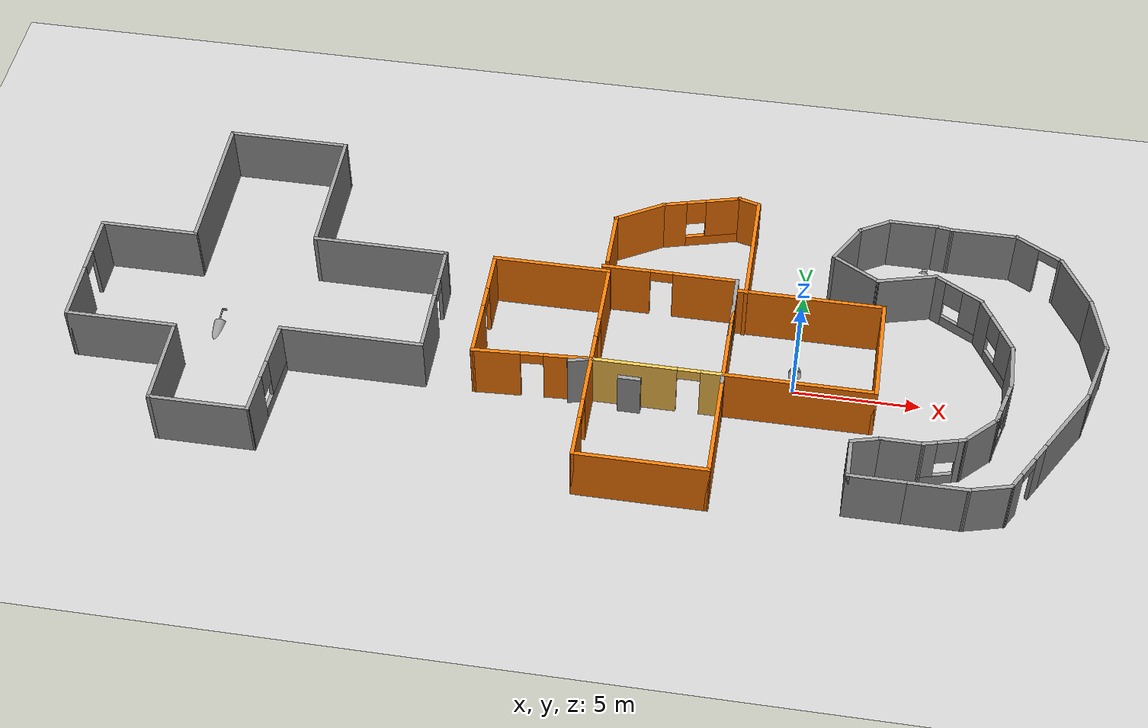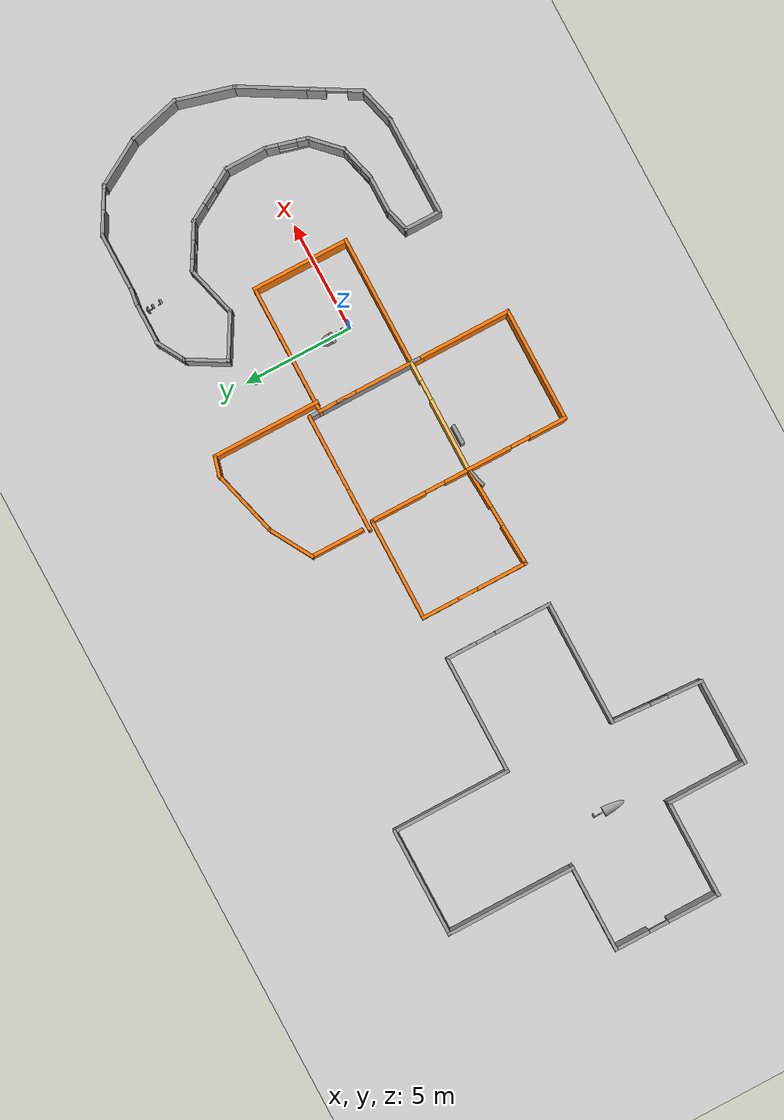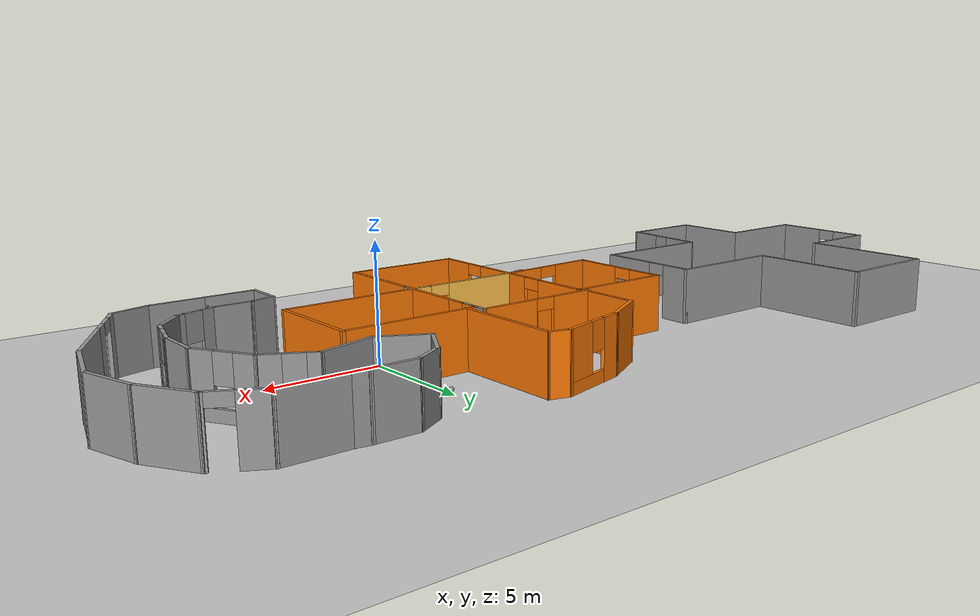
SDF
<sdf version="1.6">
 <world name="default">
  <plugin name="welcome" filename="libwelcome.so"/>
  <light name="sun" type="directional">
   <pose>0 0 10 0 -0 0</pose>
   <diffuse>0.8 0.8 0.8 1</diffuse>
   <specular>0.2 0.2 0.2 1</specular>
   <attenuation>
    <range>1000</range>
    <constant>0.9</constant>
    <linear>0.01</linear>
    <quadratic>0.001</quadratic>
   </attenuation>
   <direction>-0.5 0.1 -0.9</direction>
  </light>
  <model name="ground_plane">
   <static>1</static>
   <link name="link">
    <collision name="collision">
     <geometry><plane><normal>0 0 1</normal><size>100 100</size></plane></geometry>
     <surface>
      <contact><collide_bitmask>65535</collide_bitmask></contact>
      <friction><ode><mu>100</mu><mu2>50</mu2></ode></friction>
     </surface>
    </collision>
    <visual name="visual">
     <cast_shadows>0</cast_shadows>
     <geometry><plane><normal>0 0 1</normal><size>100 100</size></plane></geometry>
     <material>
      <script><uri>file://media/materials/scripts/gazebo.material</uri><name>Gazebo/Grey</name></script>
     </material>
    </visual>
   </link>
  </model>
  <gravity>0 0 -9.8</gravity>
  <magnetic_field>6e-06 2.3e-05 -4.2e-05</magnetic_field>
  <atmosphere type="adiabatic"/>
  <physics name="default_physics" default="0" type="ode">
   <max_step_size>0.001</max_step_size>
   <real_time_factor>1</real_time_factor>
   <real_time_update_rate>1000</real_time_update_rate>
  </physics>
  <scene><ambient>0.4 0.4 0.4 1</ambient><background>0.7 0.7 0.7 1</background><shadows>1</shadows></scene>
  <spherical_coordinates>
   <surface_model>EARTH_WGS84</surface_model>
   <latitude_deg>0</latitude_deg>
   <longitude_deg>0</longitude_deg>
   <elevation>0</elevation>
   <heading_deg>0</heading_deg>
  </spherical_coordinates>
  <model name="Android">
   <link name="link_0_clone">
    <pose>0.077813 0.225 -0.462714 0 -0 0</pose>
    <inertial>
     <mass>1</mass>
     <inertia>
      <ixx>0.166667</ixx>
      <ixy>0</ixy>
      <ixz>0</ixz>
      <iyy>0.166667</iyy>
      <iyz>0</iyz>
      <izz>0.166667</izz>
     </inertia>
    </inertial>
    <visual name="visual">
     <geometry><box><size>0.2 0.1 0.05</size></box></geometry>
     <material>
      <lighting>1</lighting>
      <script><uri>file://media/materials/scripts/gazebo.material</uri><name>Gazebo/Grey</name></script>
      <shader type="pixel"><normal_map>__default__</normal_map></shader>
      <ambient>0.3 0.3 0.3 1</ambient>
      <diffuse>0.7 0.7 0.7 1</diffuse>
      <specular>0.01 0.01 0.01 1</specular>
      <emissive>0 0 0 1</emissive>
     </material>
    </visual>
    <collision name="collision">
     <geometry><box><size>0.2 0.1 0.05</size></box></geometry>
     <surface>
      <friction>
       <ode><mu>1</mu><mu2>1</mu2><fdir1>0 0 0</fdir1><slip1>0</slip1><slip2>0</slip2></ode>
       <torsional>
        <coefficient>1</coefficient>
        <patch_radius>0</patch_radius>
        <surface_radius>0</surface_radius>
        <use_patch_radius>1</use_patch_radius>
        <ode><slip>0</slip></ode>
       </torsional>
      </friction>
      <bounce><restitution_coefficient>0</restitution_coefficient><threshold>1e+06</threshold></bounce>
      <contact>
       <collide_without_contact>0</collide_without_contact>
       <collide_without_contact_bitmask>1</collide_without_contact_bitmask>
       <collide_bitmask>1</collide_bitmask>
       <ode>
        <soft_cfm>0</soft_cfm>
        <soft_erp>0.2</soft_erp>
        <kp>1e+13</kp>
        <kd>1</kd>
        <max_vel>0.01</max_vel>
        <min_depth>0</min_depth>
       </ode>
       <bullet>
        <split_impulse>1</split_impulse>
        <split_impulse_penetration_threshold>-0.01</split_impulse_penetration_threshold>
        <soft_cfm>0</soft_cfm>
        <soft_erp>0.2</soft_erp>
        <kp>1e+13</kp>
        <kd>1</kd>
       </bullet>
      </contact>
     </surface>
    </collision>
   </link>
   <link name="link_0_clone_clone">
    <pose>0.020312 -0.225 -0.462144 0 -0 0</pose>
    <inertial>
     <mass>1</mass>
     <inertia>
      <ixx>0.166667</ixx>
      <ixy>0</ixy>
      <ixz>0</ixz>
      <iyy>0.166667</iyy>
      <iyz>0</iyz>
      <izz>0.166667</izz>
     </inertia>
    </inertial>
    <visual name="visual">
     <geometry><box><size>0.2 0.1 0.05</size></box></geometry>
     <material>
      <lighting>1</lighting>
      <script><uri>file://media/materials/scripts/gazebo.material</uri><name>Gazebo/Grey</name></script>
      <shader type="pixel"><normal_map>__default__</normal_map></shader>
      <ambient>0.3 0.3 0.3 1</ambient>
      <diffuse>0.7 0.7 0.7 1</diffuse>
      <specular>0.01 0.01 0.01 1</specular>
      <emissive>0 0 0 1</emissive>
     </material>
    </visual>
    <collision name="collision">
     <geometry><box><size>0.2 0.1 0.05</size></box></geometry>
     <surface>
      <friction>
       <ode><mu>1</mu><mu2>1</mu2><fdir1>0 0 0</fdir1><slip1>0</slip1><slip2>0</slip2></ode>
       <torsional>
        <coefficient>1</coefficient>
        <patch_radius>0</patch_radius>
        <surface_radius>0</surface_radius>
        <use_patch_radius>1</use_patch_radius>
        <ode><slip>0</slip></ode>
       </torsional>
      </friction>
      <bounce><restitution_coefficient>0</restitution_coefficient><threshold>1e+06</threshold></bounce>
      <contact>
       <collide_without_contact>0</collide_without_contact>
       <collide_without_contact_bitmask>1</collide_without_contact_bitmask>
       <collide_bitmask>1</collide_bitmask>
       <ode>
        <soft_cfm>0</soft_cfm>
        <soft_erp>0.2</soft_erp>
        <kp>1e+13</kp>
        <kd>1</kd>
        <max_vel>0.01</max_vel>
        <min_depth>0</min_depth>
       </ode>
       <bullet>
        <split_impulse>1</split_impulse>
        <split_impulse_penetration_threshold>-0.01</split_impulse_penetration_threshold>
        <soft_cfm>0</soft_cfm>
        <soft_erp>0.2</soft_erp>
        <kp>1e+13</kp>
        <kd>1</kd>
       </bullet>
      </contact>
     </surface>
    </collision>
   </link>
   <link name="link_1">
    <pose>-0.054688 -0.225 -0.099644 0 -0 0</pose>
    <inertial>
     <mass>1</mass>
     <inertia>
      <ixx>0.166667</ixx>
      <ixy>0</ixy>
      <ixz>0</ixz>
      <iyy>0.166667</iyy>
      <iyz>0</iyz>
      <izz>0.166667</izz>
     </inertia>
    </inertial>
    <visual name="visual">
     <geometry><box><size>0.05 0.05 0.225</size></box></geometry>
     <material>
      <lighting>1</lighting>
      <script><uri>file://media/materials/scripts/gazebo.material</uri><name>Gazebo/Grey</name></script>
      <shader type="pixel"><normal_map>__default__</normal_map></shader>
      <ambient>0.3 0.3 0.3 1</ambient>
      <diffuse>0.7 0.7 0.7 1</diffuse>
      <specular>0.01 0.01 0.01 1</specular>
      <emissive>0 0 0 1</emissive>
     </material>
    </visual>
    <collision name="collision">
     <geometry><box><size>0.05 0.05 0.225</size></box></geometry>
     <surface>
      <friction>
       <ode><mu>1</mu><mu2>1</mu2><fdir1>0 0 0</fdir1><slip1>0</slip1><slip2>0</slip2></ode>
       <torsional>
        <coefficient>1</coefficient>
        <patch_radius>0</patch_radius>
        <surface_radius>0</surface_radius>
        <use_patch_radius>1</use_patch_radius>
        <ode><slip>0</slip></ode>
       </torsional>
      </friction>
      <bounce><restitution_coefficient>0</restitution_coefficient><threshold>1e+06</threshold></bounce>
      <contact>
       <collide_without_contact>0</collide_without_contact>
       <collide_without_contact_bitmask>1</collide_without_contact_bitmask>
       <collide_bitmask>1</collide_bitmask>
       <ode>
        <soft_cfm>0</soft_cfm>
        <soft_erp>0.2</soft_erp>
        <kp>1e+13</kp>
        <kd>1</kd>
        <max_vel>0.01</max_vel>
        <min_depth>0</min_depth>
       </ode>
       <bullet>
        <split_impulse>1</split_impulse>
        <split_impulse_penetration_threshold>-0.01</split_impulse_penetration_threshold>
        <soft_cfm>0</soft_cfm>
        <soft_erp>0.2</soft_erp>
        <kp>1e+13</kp>
        <kd>1</kd>
       </bullet>
      </contact>
     </surface>
    </collision>
   </link>
   <link name="link_1_clone">
    <pose>-0.054688 -0.225 -0.324644 0 -0 0</pose>
    <inertial>
     <mass>1</mass>
     <inertia>
      <ixx>0.166667</ixx>
      <ixy>0</ixy>
      <ixz>0</ixz>
      <iyy>0.166667</iyy>
      <iyz>0</iyz>
      <izz>0.166667</izz>
     </inertia>
    </inertial>
    <visual name="visual">
     <geometry><box><size>0.05 0.05 0.225</size></box></geometry>
     <material>
      <lighting>1</lighting>
      <script><uri>file://media/materials/scripts/gazebo.material</uri><name>Gazebo/Grey</name></script>
      <shader type="pixel"><normal_map>__default__</normal_map></shader>
      <ambient>0.3 0.3 0.3 1</ambient>
      <diffuse>0.7 0.7 0.7 1</diffuse>
      <specular>0.01 0.01 0.01 1</specular>
      <emissive>0 0 0 1</emissive>
     </material>
    </visual>
    <collision name="collision">
     <geometry><box><size>0.05 0.05 0.225</size></box></geometry>
     <surface>
      <friction>
       <ode><mu>1</mu><mu2>1</mu2><fdir1>0 0 0</fdir1><slip1>0</slip1><slip2>0</slip2></ode>
       <torsional>
        <coefficient>1</coefficient>
        <patch_radius>0</patch_radius>
        <surface_radius>0</surface_radius>
        <use_patch_radius>1</use_patch_radius>
        <ode><slip>0</slip></ode>
       </torsional>
      </friction>
      <bounce><restitution_coefficient>0</restitution_coefficient><threshold>1e+06</threshold></bounce>
      <contact>
       <collide_without_contact>0</collide_without_contact>
       <collide_without_contact_bitmask>1</collide_without_contact_bitmask>
       <collide_bitmask>1</collide_bitmask>
       <ode>
        <soft_cfm>0</soft_cfm>
        <soft_erp>0.2</soft_erp>
        <kp>1e+13</kp>
        <kd>1</kd>
        <max_vel>0.01</max_vel>
        <min_depth>0</min_depth>
       </ode>
       <bullet>
        <split_impulse>1</split_impulse>
        <split_impulse_penetration_threshold>-0.01</split_impulse_penetration_threshold>
        <soft_cfm>0</soft_cfm>
        <soft_erp>0.2</soft_erp>
        <kp>1e+13</kp>
        <kd>1</kd>
       </bullet>
      </contact>
     </surface>
    </collision>
   </link>
   <link name="link_1_clone_clone">
    <pose>0.002813 0.225 -0.100214 0 -0 0</pose>
    <inertial>
     <mass>1</mass>
     <inertia>
      <ixx>0.166667</ixx>
      <ixy>0</ixy>
      <ixz>0</ixz>
      <iyy>0.166667</iyy>
      <iyz>0</iyz>
      <izz>0.166667</izz>
     </inertia>
    </inertial>
    <visual name="visual">
     <geometry><box><size>0.05 0.05 0.225</size></box></geometry>
     <material>
      <lighting>1</lighting>
      <script><uri>file://media/materials/scripts/gazebo.material</uri><name>Gazebo/Grey</name></script>
      <shader type="pixel"><normal_map>__default__</normal_map></shader>
      <ambient>0.3 0.3 0.3 1</ambient>
      <diffuse>0.7 0.7 0.7 1</diffuse>
      <specular>0.01 0.01 0.01 1</specular>
      <emissive>0 0 0 1</emissive>
     </material>
    </visual>
    <collision name="collision">
     <geometry><box><size>0.05 0.05 0.225</size></box></geometry>
     <surface>
      <friction>
       <ode><mu>1</mu><mu2>1</mu2><fdir1>0 0 0</fdir1><slip1>0</slip1><slip2>0</slip2></ode>
       <torsional>
        <coefficient>1</coefficient>
        <patch_radius>0</patch_radius>
        <surface_radius>0</surface_radius>
        <use_patch_radius>1</use_patch_radius>
        <ode><slip>0</slip></ode>
       </torsional>
      </friction>
      <bounce><restitution_coefficient>0</restitution_coefficient><threshold>1e+06</threshold></bounce>
      <contact>
       <collide_without_contact>0</collide_without_contact>
       <collide_without_contact_bitmask>1</collide_without_contact_bitmask>
       <collide_bitmask>1</collide_bitmask>
       <ode>
        <soft_cfm>0</soft_cfm>
        <soft_erp>0.2</soft_erp>
        <kp>1e+13</kp>
        <kd>1</kd>
        <max_vel>0.01</max_vel>
        <min_depth>0</min_depth>
       </ode>
       <bullet>
        <split_impulse>1</split_impulse>
        <split_impulse_penetration_threshold>-0.01</split_impulse_penetration_threshold>
        <soft_cfm>0</soft_cfm>
        <soft_erp>0.2</soft_erp>
        <kp>1e+13</kp>
        <kd>1</kd>
       </bullet>
      </contact>
     </surface>
    </collision>
   </link>
   <link name="link_1_clone_clone_clone">
    <pose>0.002813 0.225 -0.325214 0 -0 0</pose>
    <inertial>
     <mass>1</mass>
     <inertia>
      <ixx>0.166667</ixx>
      <ixy>0</ixy>
      <ixz>0</ixz>
      <iyy>0.166667</iyy>
      <iyz>0</iyz>
      <izz>0.166667</izz>
     </inertia>
    </inertial>
    <visual name="visual">
     <geometry><box><size>0.05 0.05 0.225</size></box></geometry>
     <material>
      <lighting>1</lighting>
      <script><uri>file://media/materials/scripts/gazebo.material</uri><name>Gazebo/Grey</name></script>
      <shader type="pixel"><normal_map>__default__</normal_map></shader>
      <ambient>0.3 0.3 0.3 1</ambient>
      <diffuse>0.7 0.7 0.7 1</diffuse>
      <specular>0.01 0.01 0.01 1</specular>
      <emissive>0 0 0 1</emissive>
     </material>
    </visual>
    <collision name="collision">
     <geometry><box><size>0.05 0.05 0.225</size></box></geometry>
     <surface>
      <friction>
       <ode><mu>1</mu><mu2>1</mu2><fdir1>0 0 0</fdir1><slip1>0</slip1><slip2>0</slip2></ode>
       <torsional>
        <coefficient>1</coefficient>
        <patch_radius>0</patch_radius>
        <surface_radius>0</surface_radius>
        <use_patch_radius>1</use_patch_radius>
        <ode><slip>0</slip></ode>
       </torsional>
      </friction>
      <bounce><restitution_coefficient>0</restitution_coefficient><threshold>1e+06</threshold></bounce>
      <contact>
       <collide_without_contact>0</collide_without_contact>
       <collide_without_contact_bitmask>1</collide_without_contact_bitmask>
       <collide_bitmask>1</collide_bitmask>
       <ode>
        <soft_cfm>0</soft_cfm>
        <soft_erp>0.2</soft_erp>
        <kp>1e+13</kp>
        <kd>1</kd>
        <max_vel>0.01</max_vel>
        <min_depth>0</min_depth>
       </ode>
       <bullet>
        <split_impulse>1</split_impulse>
        <split_impulse_penetration_threshold>-0.01</split_impulse_penetration_threshold>
        <soft_cfm>0</soft_cfm>
        <soft_erp>0.2</soft_erp>
        <kp>1e+13</kp>
        <kd>1</kd>
       </bullet>
      </contact>
     </surface>
    </collision>
   </link>
   <link name="link_2">
    <pose>0.002813 0 0.512286 0 -0 0</pose>
    <inertial>
     <mass>1</mass>
     <inertia><ixx>0.145833</ixx><ixy>0</ixy><ixz>0</ixz><iyy>0.145833</iyy><iyz>0</iyz><izz>0.125</izz></inertia>
    </inertial>
    <visual name="visual">
     <geometry><cylinder><radius>0.25</radius><length>1</length></cylinder></geometry>
     <material>
      <lighting>1</lighting>
      <script><uri>file://media/materials/scripts/gazebo.material</uri><name>Gazebo/Grey</name></script>
      <shader type="pixel"><normal_map>__default__</normal_map></shader>
      <ambient>0.3 0.3 0.3 1</ambient>
      <diffuse>0.7 0.7 0.7 1</diffuse>
      <specular>0.01 0.01 0.01 1</specular>
      <emissive>0 0 0 1</emissive>
     </material>
    </visual>
    <collision name="collision">
     <geometry><cylinder><radius>0.25</radius><length>1</length></cylinder></geometry>
     <surface>
      <friction>
       <ode><mu>1</mu><mu2>1</mu2><fdir1>0 0 0</fdir1><slip1>0</slip1><slip2>0</slip2></ode>
       <torsional>
        <coefficient>1</coefficient>
        <patch_radius>0</patch_radius>
        <surface_radius>0</surface_radius>
        <use_patch_radius>1</use_patch_radius>
        <ode><slip>0</slip></ode>
       </torsional>
      </friction>
      <bounce><restitution_coefficient>0</restitution_coefficient><threshold>1e+06</threshold></bounce>
      <contact>
       <collide_without_contact>0</collide_without_contact>
       <collide_without_contact_bitmask>1</collide_without_contact_bitmask>
       <collide_bitmask>1</collide_bitmask>
       <ode>
        <soft_cfm>0</soft_cfm>
        <soft_erp>0.2</soft_erp>
        <kp>1e+13</kp>
        <kd>1</kd>
        <max_vel>0.01</max_vel>
        <min_depth>0</min_depth>
       </ode>
       <bullet>
        <split_impulse>1</split_impulse>
        <split_impulse_penetration_threshold>-0.01</split_impulse_penetration_threshold>
        <soft_cfm>0</soft_cfm>
        <soft_erp>0.2</soft_erp>
        <kp>1e+13</kp>
        <kd>1</kd>
       </bullet>
      </contact>
     </surface>
    </collision>
   </link>
   <link name="link_3">
    <pose>0.002813 0 1.26229 0 -0 0</pose>
    <inertial>
     <mass>1</mass>
     <inertia><ixx>0.1</ixx><ixy>0</ixy><ixz>0</ixz><iyy>0.1</iyy><iyz>0</iyz><izz>0.1</izz></inertia>
    </inertial>
    <visual name="visual">
     <geometry><sphere><radius>0.25</radius></sphere></geometry>
     <material>
      <lighting>1</lighting>
      <script><uri>file://media/materials/scripts/gazebo.material</uri><name>Gazebo/Grey</name></script>
      <shader type="pixel"><normal_map>__default__</normal_map></shader>
      <ambient>0.3 0.3 0.3 1</ambient>
      <diffuse>0.7 0.7 0.7 1</diffuse>
      <specular>0.01 0.01 0.01 1</specular>
      <emissive>0 0 0 1</emissive>
     </material>
    </visual>
    <collision name="collision">
     <geometry><sphere><radius>0.25</radius></sphere></geometry>
     <surface>
      <friction>
       <ode><mu>1</mu><mu2>1</mu2><fdir1>0 0 0</fdir1><slip1>0</slip1><slip2>0</slip2></ode>
       <torsional>
        <coefficient>1</coefficient>
        <patch_radius>0</patch_radius>
        <surface_radius>0</surface_radius>
        <use_patch_radius>1</use_patch_radius>
        <ode><slip>0</slip></ode>
       </torsional>
      </friction>
      <bounce><restitution_coefficient>0</restitution_coefficient><threshold>1e+06</threshold></bounce>
      <contact>
       <collide_without_contact>0</collide_without_contact>
       <collide_without_contact_bitmask>1</collide_without_contact_bitmask>
       <collide_bitmask>1</collide_bitmask>
       <ode>
        <soft_cfm>0</soft_cfm>
        <soft_erp>0.2</soft_erp>
        <kp>1e+13</kp>
        <kd>1</kd>
        <max_vel>0.01</max_vel>
        <min_depth>0</min_depth>
       </ode>
       <bullet>
        <split_impulse>1</split_impulse>
        <split_impulse_penetration_threshold>-0.01</split_impulse_penetration_threshold>
        <soft_cfm>0</soft_cfm>
        <soft_erp>0.2</soft_erp>
        <kp>1e+13</kp>
        <kd>1</kd>
       </bullet>
      </contact>
     </surface>
    </collision>
   </link>
   <joint name="link_1_JOINT_14" type="revolute">
    <parent>link_1</parent>
    <child>link_1_clone</child>
    <axis>
     <xyz>-1 0 0</xyz>
     <use_parent_model_frame>0</use_parent_model_frame>
     <limit>
      <lower>-1.79769e+308</lower>
      <upper>1.79769e+308</upper>
      <effort>-1</effort>
      <velocity>-1</velocity>
     </limit>
     <dynamics>
      <spring_reference>0</spring_reference>
      <spring_stiffness>0</spring_stiffness>
      <damping>0</damping>
     </dynamics>
    </axis>
    <physics>
     <ode><limit><cfm>0</cfm><erp>0.2</erp></limit><suspension><cfm>0</cfm><erp>0.2</erp></suspension></ode>
    </physics>
   </joint>
   <joint name="link_1_clone_JOINT_15" type="revolute">
    <parent>link_1_clone</parent>
    <child>link_0_clone_clone</child>
    <axis>
     <xyz>1 0 0</xyz>
     <use_parent_model_frame>0</use_parent_model_frame>
     <limit>
      <lower>-1.79769e+308</lower>
      <upper>1.79769e+308</upper>
      <effort>-1</effort>
      <velocity>-1</velocity>
     </limit>
     <dynamics>
      <spring_reference>0</spring_reference>
      <spring_stiffness>0</spring_stiffness>
      <damping>0</damping>
     </dynamics>
    </axis>
    <physics>
     <ode><limit><cfm>0</cfm><erp>0.2</erp></limit><suspension><cfm>0</cfm><erp>0.2</erp></suspension></ode>
    </physics>
   </joint>
   <joint name="link_1_clone_clone_JOINT_11" type="revolute">
    <parent>link_1_clone_clone</parent>
    <child>link_1_clone_clone_clone</child>
    <axis>
     <xyz>-1 0 0</xyz>
     <use_parent_model_frame>0</use_parent_model_frame>
     <limit>
      <lower>-1.79769e+308</lower>
      <upper>1.79769e+308</upper>
      <effort>-1</effort>
      <velocity>-1</velocity>
     </limit>
     <dynamics>
      <spring_reference>0</spring_reference>
      <spring_stiffness>0</spring_stiffness>
      <damping>0</damping>
     </dynamics>
    </axis>
    <physics>
     <ode><limit><cfm>0</cfm><erp>0.2</erp></limit><suspension><cfm>0</cfm><erp>0.2</erp></suspension></ode>
    </physics>
   </joint>
   <joint name="link_1_clone_clone_clone_JOINT_12" type="revolute">
    <parent>link_1_clone_clone_clone</parent>
    <child>link_0_clone</child>
    <axis>
     <xyz>1 0 0</xyz>
     <use_parent_model_frame>0</use_parent_model_frame>
     <limit>
      <lower>-1.79769e+308</lower>
      <upper>1.79769e+308</upper>
      <effort>-1</effort>
      <velocity>-1</velocity>
     </limit>
     <dynamics>
      <spring_reference>0</spring_reference>
      <spring_stiffness>0</spring_stiffness>
      <damping>0</damping>
     </dynamics>
    </axis>
    <physics>
     <ode><limit><cfm>0</cfm><erp>0.2</erp></limit><suspension><cfm>0</cfm><erp>0.2</erp></suspension></ode>
    </physics>
   </joint>
   <joint name="link_2_JOINT_10" type="revolute">
    <parent>link_2</parent>
    <child>link_1_clone_clone</child>
    <axis>
     <xyz>1 0 0</xyz>
     <use_parent_model_frame>0</use_parent_model_frame>
     <limit>
      <lower>-1.79769e+308</lower>
      <upper>1.79769e+308</upper>
      <effort>-1</effort>
      <velocity>-1</velocity>
     </limit>
     <dynamics>
      <spring_reference>0</spring_reference>
      <spring_stiffness>0</spring_stiffness>
      <damping>0</damping>
     </dynamics>
    </axis>
    <physics>
     <ode><limit><cfm>0</cfm><erp>0.2</erp></limit><suspension><cfm>0</cfm><erp>0.2</erp></suspension></ode>
    </physics>
   </joint>
   <joint name="link_2_JOINT_13" type="revolute">
    <parent>link_2</parent>
    <child>link_1</child>
    <axis>
     <xyz>1 0 0</xyz>
     <use_parent_model_frame>0</use_parent_model_frame>
     <limit>
      <lower>-1.79769e+308</lower>
      <upper>1.79769e+308</upper>
      <effort>-1</effort>
      <velocity>-1</velocity>
     </limit>
     <dynamics>
      <spring_reference>0</spring_reference>
      <spring_stiffness>0</spring_stiffness>
      <damping>0</damping>
     </dynamics>
    </axis>
    <physics>
     <ode><limit><cfm>0</cfm><erp>0.2</erp></limit><suspension><cfm>0</cfm><erp>0.2</erp></suspension></ode>
    </physics>
   </joint>
   <joint name="link_3_JOINT_20" type="revolute">
    <parent>link_2</parent>
    <child>link_3</child>
    <axis>
     <xyz>0 0 1</xyz>
     <use_parent_model_frame>0</use_parent_model_frame>
     <limit>
      <lower>-1.79769e+308</lower>
      <upper>1.79769e+308</upper>
      <effort>-1</effort>
      <velocity>-1</velocity>
     </limit>
     <dynamics>
      <spring_reference>0</spring_reference>
      <spring_stiffness>0</spring_stiffness>
      <damping>0</damping>
     </dynamics>
    </axis>
    <physics>
     <ode><limit><cfm>0</cfm><erp>0.2</erp></limit><suspension><cfm>0</cfm><erp>0.2</erp></suspension></ode>
    </physics>
   </joint>
   <static>0</static>
   <pose>-0.001618 0.818507 0.069668 -2.20596 -0 -0.001507</pose>
  </model>
  <model name="Cplusplus">
   <pose>-8.29888 1.0832 0 0 -0 0</pose>
   <link name="Door_1">
    <collision name="Door_1_Collision">
     <geometry><box><size>0.9 0.17 2</size></box></geometry>
     <pose>0 0 1 0 -0 0</pose>
    </collision>
    <visual name="Door_1_Visual">
     <pose>0 0 1 0 -0 0</pose>
     <geometry><box><size>0.9 0.17 2</size></box></geometry>
     <material>
      <script><uri>file://media/materials/scripts/gazebo.material</uri><name>Gazebo/Grey</name></script>
     </material>
    </visual>
    <pose>2.05873 -2.95917 0 0 -0 0</pose>
   </link>
   <link name="Wall_10">
    <pose>-4.07558 -0.465829 0 0 0 -1.5708</pose>
    <visual name="Wall_10_Visual_0">
     <pose>-1.63477 0 1.25 0 -0 0</pose>
     <geometry><box><size>1.73046 0.15 2.5</size></box></geometry>
     <material>
      <script><uri>file://media/materials/scripts/gazebo.material</uri><name>Gazebo/Grey</name></script>
      <ambient>0.996078 0.47451 0.0196078 1</ambient>
     </material>
     <meta><layer>0</layer></meta>
    </visual>
    <collision name="Wall_10_Collision_0">
     <geometry><box><size>1.73046 0.15 2.5</size></box></geometry>
     <pose>-1.63477 0 1.25 0 -0 0</pose>
    </collision>
    <visual name="Wall_10_Visual_1">
     <pose>1.31523 0 1.25 0 -0 0</pose>
     <geometry><box><size>2.36954 0.15 2.5</size></box></geometry>
     <material>
      <script><uri>file://media/materials/scripts/gazebo.material</uri><name>Gazebo/Grey</name></script>
      <ambient>0.996078 0.47451 0.0196078 1</ambient>
     </material>
     <meta><layer>0</layer></meta>
    </visual>
    <collision name="Wall_10_Collision_1">
     <geometry><box><size>2.36954 0.15 2.5</size></box></geometry>
     <pose>1.31523 0 1.25 0 -0 0</pose>
    </collision>
    <visual name="Wall_10_Visual_2">
     <pose>-0.319538 0 2.25 0 -0 0</pose>
     <geometry><box><size>0.9 0.15 0.5</size></box></geometry>
     <material>
      <script><uri>file://media/materials/scripts/gazebo.material</uri><name>Gazebo/Grey</name></script>
      <ambient>0.996078 0.47451 0.0196078 1</ambient>
     </material>
     <meta><layer>0</layer></meta>
    </visual>
    <collision name="Wall_10_Collision_2">
     <geometry><box><size>0.9 0.15 0.5</size></box></geometry>
     <pose>-0.319538 0 2.25 0 -0 0</pose>
    </collision>
   </link>
   <link name="Wall_11">
    <pose>-1.77558 -2.76583 0 0 -0 0.054294</pose>
    <visual name="Wall_11_Visual_0">
     <pose>-1.40985 0 1.25 0 -0 0</pose>
     <geometry><box><size>1.9371 0.15 2.5</size></box></geometry>
     <material>
      <script><uri>file://media/materials/scripts/gazebo.material</uri><name>Gazebo/Grey</name></script>
      <ambient>0.996078 0.47451 0.0196078 1</ambient>
     </material>
     <meta><layer>0</layer></meta>
    </visual>
    <collision name="Wall_11_Collision_0">
     <geometry><box><size>1.9371 0.15 2.5</size></box></geometry>
     <pose>-1.40985 0 1.25 0 -0 0</pose>
    </collision>
    <visual name="Wall_11_Visual_1">
     <pose>1.41855 0 1.25 0 -0 0</pose>
     <geometry><box><size>1.91969 0.15 2.5</size></box></geometry>
     <material>
      <script><uri>file://media/materials/scripts/gazebo.material</uri><name>Gazebo/Grey</name></script>
      <ambient>0.996078 0.47451 0.0196078 1</ambient>
     </material>
     <meta><layer>0</layer></meta>
    </visual>
    <collision name="Wall_11_Collision_1">
     <geometry><box><size>1.91969 0.15 2.5</size></box></geometry>
     <pose>1.41855 0 1.25 0 -0 0</pose>
    </collision>
    <visual name="Wall_11_Visual_2">
     <pose>0.008704 0 2.25 0 -0 0</pose>
     <geometry><box><size>0.9 0.15 0.5</size></box></geometry>
     <material>
      <script><uri>file://media/materials/scripts/gazebo.material</uri><name>Gazebo/Grey</name></script>
      <ambient>0.996078 0.47451 0.0196078 1</ambient>
     </material>
     <meta><layer>0</layer></meta>
    </visual>
    <collision name="Wall_11_Collision_2">
     <geometry><box><size>0.9 0.15 0.5</size></box></geometry>
     <pose>0.008704 0 2.25 0 -0 0</pose>
    </collision>
   </link>
   <link name="Wall_12">
    <collision name="Wall_12_Collision">
     <geometry><box><size>1 0.15 2.5</size></box></geometry>
     <pose>0 0 1.25 0 -0 0</pose>
    </collision>
    <visual name="Wall_12_Visual">
     <pose>0 0 1.25 0 -0 0</pose>
     <geometry><box><size>1 0.15 2.5</size></box></geometry>
     <material>
      <script><uri>file://media/materials/scripts/gazebo.material</uri><name>Gazebo/Grey</name></script>
      <ambient>0 0 0 0</ambient>
     </material>
     <meta><layer>0</layer></meta>
    </visual>
    <pose>0.113905 -2.75083 0 0 0 -2.87979</pose>
   </link>
   <link name="Wall_13">
    <pose>0.524424 -4.94083 0 0 0 -1.5708</pose>
    <visual name="Wall_13_Visual_0">
     <pose>-1.32659 0 1.25 0 -0 0</pose>
     <geometry><box><size>2.09682 0.15 2.5</size></box></geometry>
     <material>
      <script><uri>file://media/materials/scripts/gazebo.material</uri><name>Gazebo/Grey</name></script>
      <ambient>0.996078 0.47451 0.0196078 1</ambient>
     </material>
     <meta><layer>0</layer></meta>
    </visual>
    <collision name="Wall_13_Collision_0">
     <geometry><box><size>2.09682 0.15 2.5</size></box></geometry>
     <pose>-1.32659 0 1.25 0 -0 0</pose>
    </collision>
    <visual name="Wall_13_Visual_1">
     <pose>1.49841 0 1.25 0 -0 0</pose>
     <geometry><box><size>1.75318 0.15 2.5</size></box></geometry>
     <material>
      <script><uri>file://media/materials/scripts/gazebo.material</uri><name>Gazebo/Grey</name></script>
      <ambient>0.996078 0.47451 0.0196078 1</ambient>
     </material>
     <meta><layer>0</layer></meta>
    </visual>
    <collision name="Wall_13_Collision_1">
     <geometry><box><size>1.75318 0.15 2.5</size></box></geometry>
     <pose>1.49841 0 1.25 0 -0 0</pose>
    </collision>
    <visual name="Wall_13_Visual_2">
     <pose>0.171817 0 2.25 0 -0 0</pose>
     <geometry><box><size>0.9 0.15 0.5</size></box></geometry>
     <material>
      <script><uri>file://media/materials/scripts/gazebo.material</uri><name>Gazebo/Grey</name></script>
      <ambient>0.996078 0.47451 0.0196078 1</ambient>
     </material>
     <meta><layer>0</layer></meta>
    </visual>
    <collision name="Wall_13_Collision_2">
     <geometry><box><size>0.9 0.15 0.5</size></box></geometry>
     <pose>0.171817 0 2.25 0 -0 0</pose>
    </collision>
   </link>
   <link name="Wall_14">
    <collision name="Wall_14_Collision">
     <geometry><box><size>5.25 0.15 2.5</size></box></geometry>
     <pose>0 0 1.25 0 -0 0</pose>
    </collision>
    <visual name="Wall_14_Visual">
     <pose>0 0 1.25 0 -0 0</pose>
     <geometry><box><size>5.25 0.15 2.5</size></box></geometry>
     <material>
      <script><uri>file://media/materials/scripts/gazebo.material</uri><name>Gazebo/Grey</name></script>
      <ambient>0.996078 0.47451 0.0196078 1</ambient>
     </material>
     <meta><layer>0</layer></meta>
    </visual>
    <pose>3.07442 -7.24083 0 0 -0 0</pose>
   </link>
   <link name="Wall_15">
    <collision name="Wall_15_Collision">
     <geometry><box><size>4.25 0.15 2.5</size></box></geometry>
     <pose>0 0 1.25 0 -0 0</pose>
    </collision>
    <visual name="Wall_15_Visual">
     <pose>0 0 1.25 0 -0 0</pose>
     <geometry><box><size>4.25 0.15 2.5</size></box></geometry>
     <material>
      <script><uri>file://media/materials/scripts/gazebo.material</uri><name>Gazebo/Grey</name></script>
      <ambient>0.996078 0.47451 0.0196078 1</ambient>
     </material>
     <meta><layer>0</layer></meta>
    </visual>
    <pose>5.62442 -5.19083 0 0 -0 1.5708</pose>
   </link>
   <link name="Wall_16">
    <collision name="Wall_16_Collision">
     <geometry><box><size>0.65 0.15 2.5</size></box></geometry>
     <pose>0 0 1.25 0 -0 0</pose>
    </collision>
    <visual name="Wall_16_Visual">
     <pose>0 0 1.25 0 -0 0</pose>
     <geometry><box><size>0.65 0.15 2.5</size></box></geometry>
     <material>
      <script><uri>file://media/materials/scripts/gazebo.material</uri><name>Gazebo/Grey</name></script>
      <ambient>1 1 1 1</ambient>
     </material>
     <meta><layer>0</layer></meta>
    </visual>
    <pose>5.62442 -2.89083 0 0 -0 1.5708</pose>
   </link>
   <link name="Wall_17">
    <collision name="Wall_17_Collision">
     <geometry><box><size>6 0.15 2.5</size></box></geometry>
     <pose>0 0 1.25 0 -0 0</pose>
    </collision>
    <visual name="Wall_17_Visual">
     <pose>0 0 1.25 0 -0 0</pose>
     <geometry><box><size>6 0.15 2.5</size></box></geometry>
     <material>
      <script><uri>file://media/materials/scripts/gazebo.material</uri><name>Gazebo/Grey</name></script>
      <ambient>0.996078 0.47451 0.0196078 1</ambient>
     </material>
     <meta><layer>0</layer></meta>
    </visual>
    <pose>8.54942 -2.64083 0 0 -0 0</pose>
   </link>
   <link name="Wall_18">
    <collision name="Wall_18_Collision">
     <geometry><box><size>4.5 0.15 2.5</size></box></geometry>
     <pose>0 0 1.25 0 -0 0</pose>
    </collision>
    <visual name="Wall_18_Visual">
     <pose>0 0 1.25 0 -0 0</pose>
     <geometry><box><size>4.5 0.15 2.5</size></box></geometry>
     <material>
      <script><uri>file://media/materials/scripts/gazebo.material</uri><name>Gazebo/Grey</name></script>
      <ambient>0.996078 0.47451 0.0196078 1</ambient>
     </material>
     <meta><layer>0</layer></meta>
    </visual>
    <pose>11.4744 -0.465829 0 0 -0 1.5708</pose>
   </link>
   <link name="Wall_19">
    <collision name="Wall_19_Collision">
     <geometry><box><size>6 0.15 2.5</size></box></geometry>
     <pose>0 0 1.25 0 -0 0</pose>
    </collision>
    <visual name="Wall_19_Visual">
     <pose>0 0 1.25 0 -0 0</pose>
     <geometry><box><size>6 0.15 2.5</size></box></geometry>
     <material>
      <script><uri>file://media/materials/scripts/gazebo.material</uri><name>Gazebo/Grey</name></script>
      <ambient>0.996078 0.47451 0.0196078 1</ambient>
     </material>
     <meta><layer>0</layer></meta>
    </visual>
    <pose>8.54942 1.70917 0 0 -0 3.14159</pose>
   </link>
   <link name="Wall_20">
    <pose>5.62442 -0.715829 0 0 0 -1.5708</pose>
    <visual name="Wall_20_Visual_0">
     <pose>-2.0582 0 1.25 0 -0 0</pose>
     <geometry><box><size>0.883603 0.15 2.5</size></box></geometry>
     <material>
      <script><uri>file://media/materials/scripts/gazebo.material</uri><name>Gazebo/Grey</name></script>
      <ambient>0.996078 0.47451 0.0196078 1</ambient>
     </material>
     <meta><layer>0</layer></meta>
    </visual>
    <collision name="Wall_20_Collision_0">
     <geometry><box><size>0.883603 0.15 2.5</size></box></geometry>
     <pose>-2.0582 0 1.25 0 -0 0</pose>
    </collision>
    <visual name="Wall_20_Visual_1">
     <pose>0.891801 0 1.25 0 -0 0</pose>
     <geometry><box><size>3.2164 0.15 2.5</size></box></geometry>
     <material>
      <script><uri>file://media/materials/scripts/gazebo.material</uri><name>Gazebo/Grey</name></script>
      <ambient>0.996078 0.47451 0.0196078 1</ambient>
     </material>
     <meta><layer>0</layer></meta>
    </visual>
    <collision name="Wall_20_Collision_1">
     <geometry><box><size>3.2164 0.15 2.5</size></box></geometry>
     <pose>0.891801 0 1.25 0 -0 0</pose>
    </collision>
    <visual name="Wall_20_Visual_2">
     <pose>-1.1664 0 2.25 0 -0 0</pose>
     <geometry><box><size>0.9 0.15 0.5</size></box></geometry>
     <material>
      <script><uri>file://media/materials/scripts/gazebo.material</uri><name>Gazebo/Grey</name></script>
      <ambient>0.996078 0.47451 0.0196078 1</ambient>
     </material>
     <meta><layer>0</layer></meta>
    </visual>
    <collision name="Wall_20_Collision_2">
     <geometry><box><size>0.9 0.15 0.5</size></box></geometry>
     <pose>-1.1664 0 2.25 0 -0 0</pose>
    </collision>
   </link>
   <link name="Wall_22">
    <collision name="Wall_22_Collision">
     <geometry><box><size>2.5 0.15 2.5</size></box></geometry>
     <pose>0 0 1.25 0 -0 0</pose>
    </collision>
    <visual name="Wall_22_Visual">
     <pose>0 0 1.25 0 -0 0</pose>
     <geometry><box><size>2.5 0.15 2.5</size></box></geometry>
     <material>
      <script><uri>file://media/materials/scripts/gazebo.material</uri><name>Gazebo/Grey</name></script>
      <ambient>0.996078 0.47451 0.0196078 1</ambient>
     </material>
     <meta><layer>0</layer></meta>
    </visual>
    <pose>0.39748 3.69181 0 0 -0 1.5708</pose>
   </link>
   <link name="Wall_23">
    <collision name="Wall_23_Collision">
     <geometry><box><size>2.25 0.15 2.5</size></box></geometry>
     <pose>0 0 1.25 0 -0 0</pose>
    </collision>
    <visual name="Wall_23_Visual">
     <pose>0 0 1.25 0 -0 0</pose>
     <geometry><box><size>2.25 0.15 2.5</size></box></geometry>
     <material>
      <script><uri>file://media/materials/scripts/gazebo.material</uri><name>Gazebo/Grey</name></script>
      <ambient>0.996078 0.47451 0.0196078 1</ambient>
     </material>
     <meta><layer>0</layer></meta>
    </visual>
    <pose>1.30681 5.39181 0 0 -0 0.523599</pose>
   </link>
   <link name="Wall_24">
    <pose>3.71332 6.31798 0 0 -0 0.261799</pose>
    <visual name="Wall_24_Visual_0">
     <pose>-1.12345 0 1.25 0 -0 0</pose>
     <geometry><box><size>1.00309 0.15 2.5</size></box></geometry>
     <material>
      <script><uri>file://media/materials/scripts/gazebo.material</uri><name>Gazebo/Grey</name></script>
      <ambient>0.996078 0.47451 0.0196078 1</ambient>
     </material>
     <meta><layer>0</layer></meta>
    </visual>
    <collision name="Wall_24_Collision_0">
     <geometry><box><size>1.00309 0.15 2.5</size></box></geometry>
     <pose>-1.12345 0 1.25 0 -0 0</pose>
    </collision>
    <visual name="Wall_24_Visual_1">
     <pose>0.501546 0 0.25 0 -0 0</pose>
     <geometry><box><size>2.24691 0.15 0.5</size></box></geometry>
     <material>
      <script><uri>file://media/materials/scripts/gazebo.material</uri><name>Gazebo/Grey</name></script>
      <ambient>0.996078 0.47451 0.0196078 1</ambient>
     </material>
     <meta><layer>0</layer></meta>
    </visual>
    <collision name="Wall_24_Collision_1">
     <geometry><box><size>2.24691 0.15 0.5</size></box></geometry>
     <pose>0.501546 0 0.25 0 -0 0</pose>
    </collision>
    <visual name="Wall_24_Visual_2">
     <pose>0.901546 0 1.5 0 -0 0</pose>
     <geometry><box><size>1.44691 0.15 2</size></box></geometry>
     <material>
      <script><uri>file://media/materials/scripts/gazebo.material</uri><name>Gazebo/Grey</name></script>
      <ambient>0.996078 0.47451 0.0196078 1</ambient>
     </material>
     <meta><layer>0</layer></meta>
    </visual>
    <collision name="Wall_24_Collision_2">
     <geometry><box><size>1.44691 0.15 2</size></box></geometry>
     <pose>0.901546 0 1.5 0 -0 0</pose>
    </collision>
    <visual name="Wall_24_Visual_3">
     <pose>-0.221908 0 1.9 0 -0 0</pose>
     <geometry><box><size>0.8 0.15 1.2</size></box></geometry>
     <material>
      <script><uri>file://media/materials/scripts/gazebo.material</uri><name>Gazebo/Grey</name></script>
      <ambient>0.996078 0.47451 0.0196078 1</ambient>
     </material>
     <meta><layer>0</layer></meta>
    </visual>
    <collision name="Wall_24_Collision_3">
     <geometry><box><size>0.8 0.15 1.2</size></box></geometry>
     <pose>-0.221908 0 1.9 0 -0 0</pose>
    </collision>
   </link>
   <link name="Wall_25">
    <collision name="Wall_25_Collision">
     <geometry><box><size>1 0.15 2.5</size></box></geometry>
     <pose>0 0 1.25 0 -0 0</pose>
    </collision>
    <visual name="Wall_25_Visual">
     <pose>0 0 1.25 0 -0 0</pose>
     <geometry><box><size>1 0.15 2.5</size></box></geometry>
     <material>
      <script><uri>file://media/materials/scripts/gazebo.material</uri><name>Gazebo/Grey</name></script>
      <ambient>0.996078 0.47451 0.0196078 1</ambient>
     </material>
     <meta><layer>0</layer></meta>
    </visual>
    <pose>5.62102 6.60915 0 0 0 -0.261799</pose>
   </link>
   <link name="Wall_26">
    <collision name="Wall_26_Collision">
     <geometry><box><size>5 0.15 2.5</size></box></geometry>
     <pose>0 0 1.25 0 -0 0</pose>
    </collision>
    <visual name="Wall_26_Visual">
     <pose>0 0 1.25 0 -0 0</pose>
     <geometry><box><size>5 0.15 2.5</size></box></geometry>
     <material>
      <script><uri>file://media/materials/scripts/gazebo.material</uri><name>Gazebo/Grey</name></script>
      <ambient>0.996078 0.47451 0.0196078 1</ambient>
     </material>
     <meta><layer>0</layer></meta>
    </visual>
    <pose>6.03154 4.07415 0 0 0 -1.5708</pose>
   </link>
   <link name="Wall_28">
    <collision name="Wall_28_Collision">
     <geometry><box><size>2 0.15 2.5</size></box></geometry>
     <pose>0 0 1.25 0 -0 0</pose>
    </collision>
    <visual name="Wall_28_Visual">
     <pose>0 0 1.25 0 -0 0</pose>
     <geometry><box><size>2 0.15 2.5</size></box></geometry>
     <material>
      <script><uri>file://media/materials/scripts/gazebo.material</uri><name>Gazebo/Grey</name></script>
      <ambient>1 1 1 1</ambient>
     </material>
     <meta><layer>0</layer></meta>
    </visual>
    <pose>12.3318 6.39307 0 0 -0 3.14159</pose>
   </link>
   <link name="Wall_29">
    <collision name="Wall_29_Collision">
     <geometry><box><size>1.5 0.15 2.5</size></box></geometry>
     <pose>0 0 1.25 0 -0 0</pose>
    </collision>
    <visual name="Wall_29_Visual">
     <pose>0 0 1.25 0 -0 0</pose>
     <geometry><box><size>1.5 0.15 2.5</size></box></geometry>
     <material>
      <script><uri>file://media/materials/scripts/gazebo.material</uri><name>Gazebo/Grey</name></script>
      <ambient>1 1 1 1</ambient>
     </material>
     <meta><layer>0</layer></meta>
    </visual>
    <pose>10.8222 6.05557 0 0 0 -2.61799</pose>
   </link>
   <link name="Wall_30">
    <collision name="Wall_30_Collision">
     <geometry><box><size>2 0.15 2.5</size></box></geometry>
     <pose>0 0 1.25 0 -0 0</pose>
    </collision>
    <visual name="Wall_30_Visual">
     <pose>0 0 1.25 0 -0 0</pose>
     <geometry><box><size>2 0.15 2.5</size></box></geometry>
     <material>
      <script><uri>file://media/materials/scripts/gazebo.material</uri><name>Gazebo/Grey</name></script>
      <ambient>1 1 1 1</ambient>
     </material>
     <meta><layer>0</layer></meta>
    </visual>
    <pose>9.77517 4.91699 0 0 0 -2.0944</pose>
   </link>
   <link name="Wall_31">
    <collision name="Wall_31_Collision">
     <geometry><box><size>2.25 0.15 2.5</size></box></geometry>
     <pose>0 0 1.25 0 -0 0</pose>
    </collision>
    <visual name="Wall_31_Visual">
     <pose>0 0 1.25 0 -0 0</pose>
     <geometry><box><size>2.25 0.15 2.5</size></box></geometry>
     <material>
      <script><uri>file://media/materials/scripts/gazebo.material</uri><name>Gazebo/Grey</name></script>
      <ambient>1 1 1 1</ambient>
     </material>
     <meta><layer>0</layer></meta>
    </visual>
    <pose>10.222 3.59092 0 0 0 -0.523599</pose>
   </link>
   <link name="Wall_32">
    <collision name="Wall_32_Collision">
     <geometry><box><size>2.5 0.15 2.5</size></box></geometry>
     <pose>0 0 1.25 0 -0 0</pose>
    </collision>
    <visual name="Wall_32_Visual">
     <pose>0 0 1.25 0 -0 0</pose>
     <geometry><box><size>2.5 0.15 2.5</size></box></geometry>
     <material>
      <script><uri>file://media/materials/scripts/gazebo.material</uri><name>Gazebo/Grey</name></script>
      <ambient>1 1 1 1</ambient>
     </material>
     <meta><layer>0</layer></meta>
    </visual>
    <pose>12.2663 3.37003 0 0 -0 0.261799</pose>
   </link>
   <link name="Wall_33">
    <pose>14.3106 3.14914 0 0 0 -0.523599</pose>
    <visual name="Wall_33_Visual_0">
     <pose>-0.843094 0 1.25 0 -0 0</pose>
     <geometry><box><size>0.563813 0.15 2.5</size></box></geometry>
     <material>
      <script><uri>file://media/materials/scripts/gazebo.material</uri><name>Gazebo/Grey</name></script>
      <ambient>1 1 1 1</ambient>
     </material>
     <meta><layer>0</layer></meta>
    </visual>
    <collision name="Wall_33_Collision_0">
     <geometry><box><size>0.563813 0.15 2.5</size></box></geometry>
     <pose>-0.843094 0 1.25 0 -0 0</pose>
    </collision>
    <visual name="Wall_33_Visual_1">
     <pose>0.281906 0 0.25 0 -0 0</pose>
     <geometry><box><size>1.68619 0.15 0.5</size></box></geometry>
     <material>
      <script><uri>file://media/materials/scripts/gazebo.material</uri><name>Gazebo/Grey</name></script>
      <ambient>1 1 1 1</ambient>
     </material>
     <meta><layer>0</layer></meta>
    </visual>
    <collision name="Wall_33_Collision_1">
     <geometry><box><size>1.68619 0.15 0.5</size></box></geometry>
     <pose>0.281906 0 0.25 0 -0 0</pose>
    </collision>
    <visual name="Wall_33_Visual_2">
     <pose>0.681906 0 1.5 0 -0 0</pose>
     <geometry><box><size>0.886187 0.15 2</size></box></geometry>
     <material>
      <script><uri>file://media/materials/scripts/gazebo.material</uri><name>Gazebo/Grey</name></script>
      <ambient>1 1 1 1</ambient>
     </material>
     <meta><layer>0</layer></meta>
    </visual>
    <collision name="Wall_33_Collision_2">
     <geometry><box><size>0.886187 0.15 2</size></box></geometry>
     <pose>0.681906 0 1.5 0 -0 0</pose>
    </collision>
    <visual name="Wall_33_Visual_3">
     <pose>-0.161187 0 1.9 0 -0 0</pose>
     <geometry><box><size>0.8 0.15 1.2</size></box></geometry>
     <material>
      <script><uri>file://media/materials/scripts/gazebo.material</uri><name>Gazebo/Grey</name></script>
      <ambient>1 1 1 1</ambient>
     </material>
     <meta><layer>0</layer></meta>
    </visual>
    <collision name="Wall_33_Collision_3">
     <geometry><box><size>0.8 0.15 1.2</size></box></geometry>
     <pose>-0.161187 0 1.9 0 -0 0</pose>
    </collision>
   </link>
   <link name="Wall_34">
    <pose>15.8699 1.49831 0 0 0 -1.0472</pose>
    <visual name="Wall_34_Visual_0">
     <pose>-0.914638 0 1.25 0 -0 0</pose>
     <geometry><box><size>0.920725 0.15 2.5</size></box></geometry>
     <material>
      <script><uri>file://media/materials/scripts/gazebo.material</uri><name>Gazebo/Grey</name></script>
      <ambient>1 1 1 1</ambient>
     </material>
     <meta><layer>0</layer></meta>
    </visual>
    <collision name="Wall_34_Collision_0">
     <geometry><box><size>0.920725 0.15 2.5</size></box></geometry>
     <pose>-0.914638 0 1.25 0 -0 0</pose>
    </collision>
    <visual name="Wall_34_Visual_1">
     <pose>0.460362 0 0.25 0 -0 0</pose>
     <geometry><box><size>1.82927 0.15 0.5</size></box></geometry>
     <material>
      <script><uri>file://media/materials/scripts/gazebo.material</uri><name>Gazebo/Grey</name></script>
      <ambient>1 1 1 1</ambient>
     </material>
     <meta><layer>0</layer></meta>
    </visual>
    <collision name="Wall_34_Collision_1">
     <geometry><box><size>1.82927 0.15 0.5</size></box></geometry>
     <pose>0.460362 0 0.25 0 -0 0</pose>
    </collision>
    <visual name="Wall_34_Visual_2">
     <pose>0.860362 0 1.5 0 -0 0</pose>
     <geometry><box><size>1.02927 0.15 2</size></box></geometry>
     <material>
      <script><uri>file://media/materials/scripts/gazebo.material</uri><name>Gazebo/Grey</name></script>
      <ambient>1 1 1 1</ambient>
     </material>
     <meta><layer>0</layer></meta>
    </visual>
    <collision name="Wall_34_Collision_2">
     <geometry><box><size>1.02927 0.15 2</size></box></geometry>
     <pose>0.860362 0 1.5 0 -0 0</pose>
    </collision>
    <visual name="Wall_34_Visual_3">
     <pose>-0.054275 0 1.9 0 -0 0</pose>
     <geometry><box><size>0.8 0.15 1.2</size></box></geometry>
     <material>
      <script><uri>file://media/materials/scripts/gazebo.material</uri><name>Gazebo/Grey</name></script>
      <ambient>1 1 1 1</ambient>
     </material>
     <meta><layer>0</layer></meta>
    </visual>
    <collision name="Wall_34_Collision_3">
     <geometry><box><size>0.8 0.15 1.2</size></box></geometry>
     <pose>-0.054275 0 1.9 0 -0 0</pose>
    </collision>
   </link>
   <link name="Wall_35">
    <collision name="Wall_35_Collision">
     <geometry><box><size>2 0.15 2.5</size></box></geometry>
     <pose>0 0 1.25 0 -0 0</pose>
    </collision>
    <visual name="Wall_35_Visual">
     <pose>0 0 1.25 0 -0 0</pose>
     <geometry><box><size>2 0.15 2.5</size></box></geometry>
     <material>
      <script><uri>file://media/materials/scripts/gazebo.material</uri><name>Gazebo/Grey</name></script>
      <ambient>1 1 1 1</ambient>
     </material>
     <meta><layer>0</layer></meta>
    </visual>
    <pose>16.5199 -0.552522 0 0 0 -1.5708</pose>
   </link>
   <link name="Wall_36">
    <pose>16.2805 -2.371 0 0 0 -1.8326</pose>
    <visual name="Wall_36_Visual_0">
     <pose>-0.686343 0 1.25 0 -0 0</pose>
     <geometry><box><size>0.627315 0.15 2.5</size></box></geometry>
     <material>
      <script><uri>file://media/materials/scripts/gazebo.material</uri><name>Gazebo/Grey</name></script>
      <ambient>1 1 1 1</ambient>
     </material>
     <meta><layer>0</layer></meta>
    </visual>
    <collision name="Wall_36_Collision_0">
     <geometry><box><size>0.627315 0.15 2.5</size></box></geometry>
     <pose>-0.686343 0 1.25 0 -0 0</pose>
    </collision>
    <visual name="Wall_36_Visual_1">
     <pose>0.313657 0 0.25 0 -0 0</pose>
     <geometry><box><size>1.37268 0.15 0.5</size></box></geometry>
     <material>
      <script><uri>file://media/materials/scripts/gazebo.material</uri><name>Gazebo/Grey</name></script>
      <ambient>1 1 1 1</ambient>
     </material>
     <meta><layer>0</layer></meta>
    </visual>
    <collision name="Wall_36_Collision_1">
     <geometry><box><size>1.37268 0.15 0.5</size></box></geometry>
     <pose>0.313657 0 0.25 0 -0 0</pose>
    </collision>
    <visual name="Wall_36_Visual_2">
     <pose>0.713657 0 1.5 0 -0 0</pose>
     <geometry><box><size>0.572685 0.15 2</size></box></geometry>
     <material>
      <script><uri>file://media/materials/scripts/gazebo.material</uri><name>Gazebo/Grey</name></script>
      <ambient>1 1 1 1</ambient>
     </material>
     <meta><layer>0</layer></meta>
    </visual>
    <collision name="Wall_36_Collision_2">
     <geometry><box><size>0.572685 0.15 2</size></box></geometry>
     <pose>0.713657 0 1.5 0 -0 0</pose>
    </collision>
    <visual name="Wall_36_Visual_3">
     <pose>0.027315 0 1.9 0 -0 0</pose>
     <geometry><box><size>0.8 0.15 1.2</size></box></geometry>
     <material>
      <script><uri>file://media/materials/scripts/gazebo.material</uri><name>Gazebo/Grey</name></script>
      <ambient>1 1 1 1</ambient>
     </material>
     <meta><layer>0</layer></meta>
    </visual>
    <collision name="Wall_36_Collision_3">
     <geometry><box><size>0.8 0.15 1.2</size></box></geometry>
     <pose>0.027315 0 1.9 0 -0 0</pose>
    </collision>
   </link>
   <link name="Wall_37">
    <collision name="Wall_37_Collision">
     <geometry><box><size>1.75 0.15 2.5</size></box></geometry>
     <pose>0 0 1.25 0 -0 0</pose>
    </collision>
    <visual name="Wall_37_Visual">
     <pose>0 0 1.25 0 -0 0</pose>
     <geometry><box><size>1.75 0.15 2.5</size></box></geometry>
     <material>
      <script><uri>file://media/materials/scripts/gazebo.material</uri><name>Gazebo/Grey</name></script>
      <ambient>1 1 1 1</ambient>
     </material>
     <meta><layer>0</layer></meta>
    </visual>
    <pose>15.4754 -3.83017 0 0 0 -2.35619</pose>
   </link>
   <link name="Wall_38">
    <pose>14.137 -4.60291 0 0 0 -2.87979</pose>
    <visual name="Wall_38_Visual_0">
     <pose>-0.70207 0 1.25 0 -0 0</pose>
     <geometry><box><size>0.34586 0.15 2.5</size></box></geometry>
     <material>
      <script><uri>file://media/materials/scripts/gazebo.material</uri><name>Gazebo/Grey</name></script>
      <ambient>1 1 1 1</ambient>
     </material>
     <meta><layer>0</layer></meta>
    </visual>
    <collision name="Wall_38_Collision_0">
     <geometry><box><size>0.34586 0.15 2.5</size></box></geometry>
     <pose>-0.70207 0 1.25 0 -0 0</pose>
    </collision>
    <visual name="Wall_38_Visual_1">
     <pose>0.17293 0 0.25 0 -0 0</pose>
     <geometry><box><size>1.40414 0.15 0.5</size></box></geometry>
     <material>
      <script><uri>file://media/materials/scripts/gazebo.material</uri><name>Gazebo/Grey</name></script>
      <ambient>1 1 1 1</ambient>
     </material>
     <meta><layer>0</layer></meta>
    </visual>
    <collision name="Wall_38_Collision_1">
     <geometry><box><size>1.40414 0.15 0.5</size></box></geometry>
     <pose>0.17293 0 0.25 0 -0 0</pose>
    </collision>
    <visual name="Wall_38_Visual_2">
     <pose>0.57293 0 1.5 0 -0 0</pose>
     <geometry><box><size>0.60414 0.15 2</size></box></geometry>
     <material>
      <script><uri>file://media/materials/scripts/gazebo.material</uri><name>Gazebo/Grey</name></script>
      <ambient>1 1 1 1</ambient>
     </material>
     <meta><layer>0</layer></meta>
    </visual>
    <collision name="Wall_38_Collision_2">
     <geometry><box><size>0.60414 0.15 2</size></box></geometry>
     <pose>0.57293 0 1.5 0 -0 0</pose>
    </collision>
    <visual name="Wall_38_Visual_3">
     <pose>-0.12914 0 1.9 0 -0 0</pose>
     <geometry><box><size>0.8 0.15 1.2</size></box></geometry>
     <material>
      <script><uri>file://media/materials/scripts/gazebo.material</uri><name>Gazebo/Grey</name></script>
      <ambient>1 1 1 1</ambient>
     </material>
     <meta><layer>0</layer></meta>
    </visual>
    <collision name="Wall_38_Collision_3">
     <geometry><box><size>0.8 0.15 1.2</size></box></geometry>
     <pose>-0.12914 0 1.9 0 -0 0</pose>
    </collision>
   </link>
   <link name="Wall_39">
    <collision name="Wall_39_Collision">
     <geometry><box><size>1.75 0.15 2.5</size></box></geometry>
     <pose>0 0 1.25 0 -0 0</pose>
    </collision>
    <visual name="Wall_39_Visual">
     <pose>0 0 1.25 0 -0 0</pose>
     <geometry><box><size>1.75 0.15 2.5</size></box></geometry>
     <material>
      <script><uri>file://media/materials/scripts/gazebo.material</uri><name>Gazebo/Grey</name></script>
      <ambient>1 1 1 1</ambient>
     </material>
     <meta><layer>0</layer></meta>
    </visual>
    <pose>12.5642 -4.80997 0 0 -0 3.14159</pose>
   </link>
   <link name="Wall_40">
    <collision name="Wall_40_Collision">
     <geometry><box><size>1.25 0.15 2.5</size></box></geometry>
     <pose>0 0 1.25 0 -0 0</pose>
    </collision>
    <visual name="Wall_40_Visual">
     <pose>0 0 1.25 0 -0 0</pose>
     <geometry><box><size>1.25 0.15 2.5</size></box></geometry>
     <material>
      <script><uri>file://media/materials/scripts/gazebo.material</uri><name>Gazebo/Grey</name></script>
      <ambient>1 1 1 1</ambient>
     </material>
     <meta><layer>0</layer></meta>
    </visual>
    <pose>11.233 -4.95232 0 0 0 -2.87979</pose>
   </link>
   <link name="Wall_41">
    <collision name="Wall_41_Collision">
     <geometry><box><size>1.75 0.15 2.5</size></box></geometry>
     <pose>0 0 1.25 0 -0 0</pose>
    </collision>
    <visual name="Wall_41_Visual">
     <pose>0 0 1.25 0 -0 0</pose>
     <geometry><box><size>1.75 0.15 2.5</size></box></geometry>
     <material>
      <script><uri>file://media/materials/scripts/gazebo.material</uri><name>Gazebo/Grey</name></script>
      <ambient>1 1 1 1</ambient>
     </material>
     <meta><layer>0</layer></meta>
    </visual>
    <pose>10.7017 -5.89467 0 0 0 -1.5708</pose>
   </link>
   <link name="Wall_42">
    <collision name="Wall_42_Collision">
     <geometry><box><size>2.25 0.15 2.5</size></box></geometry>
     <pose>0 0 1.25 0 -0 0</pose>
    </collision>
    <visual name="Wall_42_Visual">
     <pose>0 0 1.25 0 -0 0</pose>
     <geometry><box><size>2.25 0.15 2.5</size></box></geometry>
     <material>
      <script><uri>file://media/materials/scripts/gazebo.material</uri><name>Gazebo/Grey</name></script>
      <ambient>1 1 1 1</ambient>
     </material>
     <meta><layer>0</layer></meta>
    </visual>
    <pose>11.7517 -6.69467 0 0 -0 0</pose>
   </link>
   <link name="Wall_43">
    <collision name="Wall_43_Collision">
     <geometry><box><size>2.5 0.15 2.5</size></box></geometry>
     <pose>0 0 1.25 0 -0 0</pose>
    </collision>
    <visual name="Wall_43_Visual">
     <pose>0 0 1.25 0 -0 0</pose>
     <geometry><box><size>2.5 0.15 2.5</size></box></geometry>
     <material>
      <script><uri>file://media/materials/scripts/gazebo.material</uri><name>Gazebo/Grey</name></script>
      <ambient>1 1 1 1</ambient>
     </material>
     <meta><layer>0</layer></meta>
    </visual>
    <pose>13.9767 -6.69467 0 0 -0 0</pose>
   </link>
   <link name="Wall_44">
    <collision name="Wall_44_Collision">
     <geometry><box><size>1.75 0.15 2.5</size></box></geometry>
     <pose>0 0 1.25 0 -0 0</pose>
    </collision>
    <visual name="Wall_44_Visual">
     <pose>0 0 1.25 0 -0 0</pose>
     <geometry><box><size>1.75 0.15 2.5</size></box></geometry>
     <material>
      <script><uri>file://media/materials/scripts/gazebo.material</uri><name>Gazebo/Grey</name></script>
      <ambient>1 1 1 1</ambient>
     </material>
     <meta><layer>0</layer></meta>
    </visual>
    <pose>15.9245 -6.48761 0 0 -0 0.261799</pose>
   </link>
   <link name="Wall_45">
    <pose>17.2847 -5.26298 0 0 -0 1.0472</pose>
    <visual name="Wall_45_Visual_0">
     <pose>-0.860729 0 1.25 0 -0 0</pose>
     <geometry><box><size>0.778542 0.15 2.5</size></box></geometry>
     <material>
      <script><uri>file://media/materials/scripts/gazebo.material</uri><name>Gazebo/Grey</name></script>
      <ambient>1 1 1 1</ambient>
     </material>
     <meta><layer>0</layer></meta>
    </visual>
    <collision name="Wall_45_Collision_0">
     <geometry><box><size>0.778542 0.15 2.5</size></box></geometry>
     <pose>-0.860729 0 1.25 0 -0 0</pose>
    </collision>
    <visual name="Wall_45_Visual_1">
     <pose>0.839271 0 1.25 0 -0 0</pose>
     <geometry><box><size>0.821458 0.15 2.5</size></box></geometry>
     <material>
      <script><uri>file://media/materials/scripts/gazebo.material</uri><name>Gazebo/Grey</name></script>
      <ambient>1 1 1 1</ambient>
     </material>
     <meta><layer>0</layer></meta>
    </visual>
    <collision name="Wall_45_Collision_1">
     <geometry><box><size>0.821458 0.15 2.5</size></box></geometry>
     <pose>0.839271 0 1.25 0 -0 0</pose>
    </collision>
    <visual name="Wall_45_Visual_2">
     <pose>-0.021458 0 2.25 0 -0 0</pose>
     <geometry><box><size>0.9 0.15 0.5</size></box></geometry>
     <material>
      <script><uri>file://media/materials/scripts/gazebo.material</uri><name>Gazebo/Grey</name></script>
      <ambient>1 1 1 1</ambient>
     </material>
     <meta><layer>0</layer></meta>
    </visual>
    <collision name="Wall_45_Collision_2">
     <geometry><box><size>0.9 0.15 0.5</size></box></geometry>
     <pose>-0.021458 0 2.25 0 -0 0</pose>
    </collision>
   </link>
   <link name="Wall_46">
    <collision name="Wall_46_Collision">
     <geometry><box><size>3.25 0.15 2.5</size></box></geometry>
     <pose>0 0 1.25 0 -0 0</pose>
    </collision>
    <visual name="Wall_46_Visual">
     <pose>0 0 1.25 0 -0 0</pose>
     <geometry><box><size>3.25 0.15 2.5</size></box></geometry>
     <material>
      <script><uri>file://media/materials/scripts/gazebo.material</uri><name>Gazebo/Grey</name></script>
      <ambient>1 1 1 1</ambient>
     </material>
     <meta><layer>0</layer></meta>
    </visual>
    <pose>18.6472 -2.90306 0 0 -0 1.0472</pose>
   </link>
   <link name="Wall_47">
    <collision name="Wall_47_Collision">
     <geometry><box><size>2.75 0.15 2.5</size></box></geometry>
     <pose>0 0 1.25 0 -0 0</pose>
    </collision>
    <visual name="Wall_47_Visual">
     <pose>0 0 1.25 0 -0 0</pose>
     <geometry><box><size>2.75 0.15 2.5</size></box></geometry>
     <material>
      <script><uri>file://media/materials/scripts/gazebo.material</uri><name>Gazebo/Grey</name></script>
      <ambient>1 1 1 1</ambient>
     </material>
     <meta><layer>0</layer></meta>
    </visual>
    <pose>19.7587 -0.305015 0 0 -0 1.309</pose>
   </link>
   <link name="Wall_48">
    <collision name="Wall_48_Collision">
     <geometry><box><size>2.5 0.15 2.5</size></box></geometry>
     <pose>0 0 1.25 0 -0 0</pose>
    </collision>
    <visual name="Wall_48_Visual">
     <pose>0 0 1.25 0 -0 0</pose>
     <geometry><box><size>2.5 0.15 2.5</size></box></geometry>
     <material>
      <script><uri>file://media/materials/scripts/gazebo.material</uri><name>Gazebo/Grey</name></script>
      <ambient>1 1 1 1</ambient>
     </material>
     <meta><layer>0</layer></meta>
    </visual>
    <pose>19.791 2.08565 0 0 -0 1.8326</pose>
   </link>
   <link name="Wall_49">
    <collision name="Wall_49_Collision">
     <geometry><box><size>2.5 0.15 2.5</size></box></geometry>
     <pose>0 0 1.25 0 -0 0</pose>
    </collision>
    <visual name="Wall_49_Visual">
     <pose>0 0 1.25 0 -0 0</pose>
     <geometry><box><size>2.5 0.15 2.5</size></box></geometry>
     <material>
      <script><uri>file://media/materials/scripts/gazebo.material</uri><name>Gazebo/Grey</name></script>
      <ambient>1 1 1 1</ambient>
     </material>
     <meta><layer>0</layer></meta>
    </visual>
    <pose>18.8994 4.23819 0 0 -0 2.0944</pose>
   </link>
   <link name="Wall_5">
    <pose>2.94942 2.20917 0 0 -0 0</pose>
    <visual name="Wall_5_Visual_0">
     <pose>-1.76993 0 1.25 0 -0 0</pose>
     <geometry><box><size>1.96013 0.15 2.5</size></box></geometry>
     <material>
      <script><uri>file://media/materials/scripts/gazebo.material</uri><name>Gazebo/Grey</name></script>
      <ambient>0.996078 0.47451 0.0196078 1</ambient>
     </material>
     <meta><layer>0</layer></meta>
    </visual>
    <collision name="Wall_5_Collision_0">
     <geometry><box><size>1.96013 0.15 2.5</size></box></geometry>
     <pose>-1.76993 0 1.25 0 -0 0</pose>
    </collision>
    <visual name="Wall_5_Visual_1">
     <pose>1.43007 0 1.25 0 -0 0</pose>
     <geometry><box><size>2.63987 0.15 2.5</size></box></geometry>
     <material>
      <script><uri>file://media/materials/scripts/gazebo.material</uri><name>Gazebo/Grey</name></script>
      <ambient>0.996078 0.47451 0.0196078 1</ambient>
     </material>
     <meta><layer>0</layer></meta>
    </visual>
    <collision name="Wall_5_Collision_1">
     <geometry><box><size>2.63987 0.15 2.5</size></box></geometry>
     <pose>1.43007 0 1.25 0 -0 0</pose>
    </collision>
    <visual name="Wall_5_Visual_2">
     <pose>-0.339868 0 2.25 0 -0 0</pose>
     <geometry><box><size>0.9 0.15 0.5</size></box></geometry>
     <material>
      <script><uri>file://media/materials/scripts/gazebo.material</uri><name>Gazebo/Grey</name></script>
      <ambient>0.996078 0.47451 0.0196078 1</ambient>
     </material>
     <meta><layer>0</layer></meta>
    </visual>
    <collision name="Wall_5_Collision_2">
     <geometry><box><size>0.9 0.15 0.5</size></box></geometry>
     <pose>-0.339868 0 2.25 0 -0 0</pose>
    </collision>
   </link>
   <link name="Wall_50">
    <pose>17.4026 5.78077 0 0 -0 2.61799</pose>
    <visual name="Wall_50_Visual_0">
     <pose>-1.02593 0 1.25 0 -0 0</pose>
     <geometry><box><size>0.198148 0.15 2.5</size></box></geometry>
     <material>
      <script><uri>file://media/materials/scripts/gazebo.material</uri><name>Gazebo/Grey</name></script>
      <ambient>1 1 1 1</ambient>
     </material>
     <meta><layer>0</layer></meta>
    </visual>
    <collision name="Wall_50_Collision_0">
     <geometry><box><size>0.198148 0.15 2.5</size></box></geometry>
     <pose>-1.02593 0 1.25 0 -0 0</pose>
    </collision>
    <visual name="Wall_50_Visual_1">
     <pose>0.549074 0 1.25 0 -0 0</pose>
     <geometry><box><size>1.15185 0.15 2.5</size></box></geometry>
     <material>
      <script><uri>file://media/materials/scripts/gazebo.material</uri><name>Gazebo/Grey</name></script>
      <ambient>1 1 1 1</ambient>
     </material>
     <meta><layer>0</layer></meta>
    </visual>
    <collision name="Wall_50_Collision_1">
     <geometry><box><size>1.15185 0.15 2.5</size></box></geometry>
     <pose>0.549074 0 1.25 0 -0 0</pose>
    </collision>
    <visual name="Wall_50_Visual_2">
     <pose>-0.476852 0 2.25 0 -0 0</pose>
     <geometry><box><size>0.9 0.15 0.5</size></box></geometry>
     <material>
      <script><uri>file://media/materials/scripts/gazebo.material</uri><name>Gazebo/Grey</name></script>
      <ambient>1 1 1 1</ambient>
     </material>
     <meta><layer>0</layer></meta>
    </visual>
    <collision name="Wall_50_Collision_2">
     <geometry><box><size>0.9 0.15 0.5</size></box></geometry>
     <pose>-0.476852 0 2.25 0 -0 0</pose>
    </collision>
   </link>
   <link name="Wall_51">
    <collision name="Wall_51_Collision">
     <geometry><box><size>2.75 0.15 2.5</size></box></geometry>
     <pose>0 0 1.25 0 -0 0</pose>
    </collision>
    <visual name="Wall_51_Visual">
     <pose>0 0 1.25 0 -0 0</pose>
     <geometry><box><size>2.75 0.15 2.5</size></box></geometry>
     <material>
      <script><uri>file://media/materials/scripts/gazebo.material</uri><name>Gazebo/Grey</name></script>
      <ambient>1 1 1 1</ambient>
     </material>
     <meta><layer>0</layer></meta>
    </visual>
    <pose>15.1933 6.30577 0 0 -0 3.14159</pose>
   </link>
   <link name="Wall_52">
    <collision name="Wall_52_Collision">
     <geometry><box><size>0.792403 0.15 2.5</size></box></geometry>
     <pose>0 0 1.25 0 -0 0</pose>
    </collision>
    <visual name="Wall_52_Visual">
     <pose>0 0 1.25 0 -0 0</pose>
     <geometry><box><size>0.792403 0.15 2.5</size></box></geometry>
     <material>
      <script><uri>file://media/materials/scripts/gazebo.material</uri><name>Gazebo/Grey</name></script>
      <ambient>1 1 1 1</ambient>
     </material>
     <meta><layer>0</layer></meta>
    </visual>
    <pose>13.575 6.34942 0 0 -0 3.00529</pose>
   </link>
   <link name="Wall_54">
    <collision name="Wall_54_Collision">
     <geometry><box><size>5.75 0.15 2.5</size></box></geometry>
     <pose>0 0 1.25 0 -0 0</pose>
    </collision>
    <visual name="Wall_54_Visual">
     <pose>0 0 1.25 0 -0 0</pose>
     <geometry><box><size>5.75 0.15 2.5</size></box></geometry>
     <material>
      <script><uri>file://media/materials/scripts/gazebo.material</uri><name>Gazebo/Grey</name></script>
      <ambient>1 1 1 1</ambient>
     </material>
     <meta><layer>0</layer></meta>
    </visual>
    <pose>-8.86198 -2.95917 0 0 -0 0</pose>
   </link>
   <link name="Wall_55">
    <pose>-6.06198 -0.534171 0 0 -0 1.5708</pose>
    <visual name="Wall_55_Visual_0">
     <pose>-1.17492 0 1.25 0 -0 0</pose>
     <geometry><box><size>2.65015 0.15 2.5</size></box></geometry>
     <material>
      <script><uri>file://media/materials/scripts/gazebo.material</uri><name>Gazebo/Grey</name></script>
      <ambient>1 1 1 1</ambient>
     </material>
     <meta><layer>0</layer></meta>
    </visual>
    <collision name="Wall_55_Collision_0">
     <geometry><box><size>2.65015 0.15 2.5</size></box></geometry>
     <pose>-1.17492 0 1.25 0 -0 0</pose>
    </collision>
    <visual name="Wall_55_Visual_1">
     <pose>1.77507 0 1.25 0 -0 0</pose>
     <geometry><box><size>1.44985 0.15 2.5</size></box></geometry>
     <material>
      <script><uri>file://media/materials/scripts/gazebo.material</uri><name>Gazebo/Grey</name></script>
      <ambient>1 1 1 1</ambient>
     </material>
     <meta><layer>0</layer></meta>
    </visual>
    <collision name="Wall_55_Collision_1">
     <geometry><box><size>1.44985 0.15 2.5</size></box></geometry>
     <pose>1.77507 0 1.25 0 -0 0</pose>
    </collision>
    <visual name="Wall_55_Visual_2">
     <pose>0.600151 0 2.25 0 -0 0</pose>
     <geometry><box><size>0.9 0.15 0.5</size></box></geometry>
     <material>
      <script><uri>file://media/materials/scripts/gazebo.material</uri><name>Gazebo/Grey</name></script>
      <ambient>1 1 1 1</ambient>
     </material>
     <meta><layer>0</layer></meta>
    </visual>
    <collision name="Wall_55_Collision_2">
     <geometry><box><size>0.9 0.15 0.5</size></box></geometry>
     <pose>0.600151 0 2.25 0 -0 0</pose>
    </collision>
   </link>
   <link name="Wall_56">
    <collision name="Wall_56_Collision">
     <geometry><box><size>5.5 0.15 2.5</size></box></geometry>
     <pose>0 0 1.25 0 -0 0</pose>
    </collision>
    <visual name="Wall_56_Visual">
     <pose>0 0 1.25 0 -0 0</pose>
     <geometry><box><size>5.5 0.15 2.5</size></box></geometry>
     <material>
      <script><uri>file://media/materials/scripts/gazebo.material</uri><name>Gazebo/Grey</name></script>
      <ambient>1 1 1 1</ambient>
     </material>
     <meta><layer>0</layer></meta>
    </visual>
    <pose>-8.73698 1.89083 0 0 -0 3.14159</pose>
   </link>
   <link name="Wall_57">
    <collision name="Wall_57_Collision">
     <geometry><box><size>5.5 0.15 2.5</size></box></geometry>
     <pose>0 0 1.25 0 -0 0</pose>
    </collision>
    <visual name="Wall_57_Visual">
     <pose>0 0 1.25 0 -0 0</pose>
     <geometry><box><size>5.5 0.15 2.5</size></box></geometry>
     <material>
      <script><uri>file://media/materials/scripts/gazebo.material</uri><name>Gazebo/Grey</name></script>
      <ambient>1 1 1 1</ambient>
     </material>
     <meta><layer>0</layer></meta>
    </visual>
    <pose>-11.412 4.56583 0 0 -0 1.5708</pose>
   </link>
   <link name="Wall_58">
    <collision name="Wall_58_Collision">
     <geometry><box><size>5 0.15 2.5</size></box></geometry>
     <pose>0 0 1.25 0 -0 0</pose>
    </collision>
    <visual name="Wall_58_Visual">
     <pose>0 0 1.25 0 -0 0</pose>
     <geometry><box><size>5 0.15 2.5</size></box></geometry>
     <material>
      <script><uri>file://media/materials/scripts/gazebo.material</uri><name>Gazebo/Grey</name></script>
      <ambient>1 1 1 1</ambient>
     </material>
     <meta><layer>0</layer></meta>
    </visual>
    <pose>-13.837 7.24083 0 0 -0 3.14159</pose>
   </link>
   <link name="Wall_59">
    <collision name="Wall_59_Collision">
     <geometry><box><size>6 0.15 2.5</size></box></geometry>
     <pose>0 0 1.25 0 -0 0</pose>
    </collision>
    <visual name="Wall_59_Visual">
     <pose>0 0 1.25 0 -0 0</pose>
     <geometry><box><size>6 0.15 2.5</size></box></geometry>
     <material>
      <script><uri>file://media/materials/scripts/gazebo.material</uri><name>Gazebo/Grey</name></script>
      <ambient>1 1 1 1</ambient>
     </material>
     <meta><layer>0</layer></meta>
    </visual>
    <pose>-16.262 4.31583 0 0 0 -1.5708</pose>
   </link>
   <link name="Wall_6">
    <collision name="Wall_6_Collision">
     <geometry><box><size>5 0.15 2.5</size></box></geometry>
     <pose>0 0 1.25 0 -0 0</pose>
    </collision>
    <visual name="Wall_6_Visual">
     <pose>0 0 1.25 0 -0 0</pose>
     <geometry><box><size>5 0.15 2.5</size></box></geometry>
     <material>
      <script><uri>file://media/materials/scripts/gazebo.material</uri><name>Gazebo/Grey</name></script>
      <ambient>1 1 1 1</ambient>
     </material>
     <meta><layer>0</layer></meta>
    </visual>
    <pose>5.62442 -0.215829 0 0 0 -1.5708</pose>
   </link>
   <link name="Wall_60">
    <collision name="Wall_60_Collision">
     <geometry><box><size>4 0.15 2.5</size></box></geometry>
     <pose>0 0 1.25 0 -0 0</pose>
    </collision>
    <visual name="Wall_60_Visual">
     <pose>0 0 1.25 0 -0 0</pose>
     <geometry><box><size>4 0.15 2.5</size></box></geometry>
     <material>
      <script><uri>file://media/materials/scripts/gazebo.material</uri><name>Gazebo/Grey</name></script>
      <ambient>1 1 1 1</ambient>
     </material>
     <meta><layer>0</layer></meta>
    </visual>
    <pose>-18.187 1.39083 0 0 -0 3.14159</pose>
   </link>
   <link name="Wall_61">
    <pose>-20.112 -1.03417 0 0 0 -1.5708</pose>
    <visual name="Wall_61_Visual_0">
     <pose>-1.67129 0 1.25 0 -0 0</pose>
     <geometry><box><size>1.65742 0.15 2.5</size></box></geometry>
     <material>
      <script><uri>file://media/materials/scripts/gazebo.material</uri><name>Gazebo/Grey</name></script>
      <ambient>1 1 1 1</ambient>
     </material>
     <meta><layer>0</layer></meta>
    </visual>
    <collision name="Wall_61_Collision_0">
     <geometry><box><size>1.65742 0.15 2.5</size></box></geometry>
     <pose>-1.67129 0 1.25 0 -0 0</pose>
    </collision>
    <visual name="Wall_61_Visual_1">
     <pose>1.27871 0 1.25 0 -0 0</pose>
     <geometry><box><size>2.44258 0.15 2.5</size></box></geometry>
     <material>
      <script><uri>file://media/materials/scripts/gazebo.material</uri><name>Gazebo/Grey</name></script>
      <ambient>1 1 1 1</ambient>
     </material>
     <meta><layer>0</layer></meta>
    </visual>
    <collision name="Wall_61_Collision_1">
     <geometry><box><size>2.44258 0.15 2.5</size></box></geometry>
     <pose>1.27871 0 1.25 0 -0 0</pose>
    </collision>
    <visual name="Wall_61_Visual_2">
     <pose>-0.39258 0 2.25 0 -0 0</pose>
     <geometry><box><size>0.9 0.15 0.5</size></box></geometry>
     <material>
      <script><uri>file://media/materials/scripts/gazebo.material</uri><name>Gazebo/Grey</name></script>
      <ambient>1 1 1 1</ambient>
     </material>
     <meta><layer>0</layer></meta>
    </visual>
    <collision name="Wall_61_Collision_2">
     <geometry><box><size>0.9 0.15 0.5</size></box></geometry>
     <pose>-0.39258 0 2.25 0 -0 0</pose>
    </collision>
   </link>
   <link name="Wall_62">
    <collision name="Wall_62_Collision">
     <geometry><box><size>4.5 0.15 2.5</size></box></geometry>
     <pose>0 0 1.25 0 -0 0</pose>
    </collision>
    <visual name="Wall_62_Visual">
     <pose>0 0 1.25 0 -0 0</pose>
     <geometry><box><size>4.5 0.15 2.5</size></box></geometry>
     <material>
      <script><uri>file://media/materials/scripts/gazebo.material</uri><name>Gazebo/Grey</name></script>
      <ambient>1 1 1 1</ambient>
     </material>
     <meta><layer>0</layer></meta>
    </visual>
    <pose>-17.937 -3.45917 0 0 -0 0</pose>
   </link>
   <link name="Wall_63">
    <collision name="Wall_63_Collision">
     <geometry><box><size>3.75 0.15 2.5</size></box></geometry>
     <pose>0 0 1.25 0 -0 0</pose>
    </collision>
    <visual name="Wall_63_Visual">
     <pose>0 0 1.25 0 -0 0</pose>
     <geometry><box><size>3.75 0.15 2.5</size></box></geometry>
     <material>
      <script><uri>file://media/materials/scripts/gazebo.material</uri><name>Gazebo/Grey</name></script>
      <ambient>1 1 1 1</ambient>
     </material>
     <meta><layer>0</layer></meta>
    </visual>
    <pose>-15.762 -5.25917 0 0 0 -1.5708</pose>
   </link>
   <link name="Wall_64">
    <collision name="Wall_64_Collision">
     <geometry><box><size>4 0.15 2.5</size></box></geometry>
     <pose>0 0 1.25 0 -0 0</pose>
    </collision>
    <visual name="Wall_64_Visual">
     <pose>0 0 1.25 0 -0 0</pose>
     <geometry><box><size>4 0.15 2.5</size></box></geometry>
     <material>
      <script><uri>file://media/materials/scripts/gazebo.material</uri><name>Gazebo/Grey</name></script>
      <ambient>1 1 1 1</ambient>
     </material>
     <meta><layer>0</layer></meta>
    </visual>
    <pose>-13.837 -7.05917 0 0 -0 0</pose>
   </link>
   <link name="Wall_65">
    <pose>-11.787 -5.00917 0 0 -0 1.5099</pose>
    <visual name="Wall_65_Visual_0">
     <pose>-1.31411 0 1.25 0 -0 0</pose>
     <geometry><box><size>1.62939 0.15 2.5</size></box></geometry>
     <material>
      <script><uri>file://media/materials/scripts/gazebo.material</uri><name>Gazebo/Grey</name></script>
      <ambient>1 1 1 1</ambient>
     </material>
     <meta><layer>0</layer></meta>
    </visual>
    <collision name="Wall_65_Collision_0">
     <geometry><box><size>1.62939 0.15 2.5</size></box></geometry>
     <pose>-1.31411 0 1.25 0 -0 0</pose>
    </collision>
    <visual name="Wall_65_Visual_1">
     <pose>0.814693 0 0.25 0 -0 0</pose>
     <geometry><box><size>2.62823 0.15 0.5</size></box></geometry>
     <material>
      <script><uri>file://media/materials/scripts/gazebo.material</uri><name>Gazebo/Grey</name></script>
      <ambient>1 1 1 1</ambient>
     </material>
     <meta><layer>0</layer></meta>
    </visual>
    <collision name="Wall_65_Collision_1">
     <geometry><box><size>2.62823 0.15 0.5</size></box></geometry>
     <pose>0.814693 0 0.25 0 -0 0</pose>
    </collision>
    <visual name="Wall_65_Visual_2">
     <pose>1.21469 0 1.5 0 -0 0</pose>
     <geometry><box><size>1.82823 0.15 2</size></box></geometry>
     <material>
      <script><uri>file://media/materials/scripts/gazebo.material</uri><name>Gazebo/Grey</name></script>
      <ambient>1 1 1 1</ambient>
     </material>
     <meta><layer>0</layer></meta>
    </visual>
    <collision name="Wall_65_Collision_2">
     <geometry><box><size>1.82823 0.15 2</size></box></geometry>
     <pose>1.21469 0 1.5 0 -0 0</pose>
    </collision>
    <visual name="Wall_65_Visual_3">
     <pose>-0.099421 0 1.9 0 -0 0</pose>
     <geometry><box><size>0.8 0.15 1.2</size></box></geometry>
     <material>
      <script><uri>file://media/materials/scripts/gazebo.material</uri><name>Gazebo/Grey</name></script>
      <ambient>1 1 1 1</ambient>
     </material>
     <meta><layer>0</layer></meta>
    </visual>
    <collision name="Wall_65_Collision_3">
     <geometry><box><size>0.8 0.15 1.2</size></box></geometry>
     <pose>-0.099421 0 1.9 0 -0 0</pose>
    </collision>
   </link>
   <link name="Wall_7">
    <pose>3.07442 -2.64083 0 0 -0 3.14159</pose>
    <visual name="Wall_7_Visual_0">
     <pose>-2.15463 0 1.25 0 -0 0</pose>
     <geometry><box><size>0.940734 0.15 2.5</size></box></geometry>
     <material>
      <script><uri>file://media/materials/scripts/gazebo.material</uri><name>Gazebo/Grey</name></script>
      <ambient>1 0.764706 0.305882 1</ambient>
     </material>
     <meta><layer>0</layer></meta>
    </visual>
    <collision name="Wall_7_Collision_0">
     <geometry><box><size>0.940734 0.15 2.5</size></box></geometry>
     <pose>-2.15463 0 1.25 0 -0 0</pose>
    </collision>
    <visual name="Wall_7_Visual_1">
     <pose>0.920367 0 1.25 0 -0 0</pose>
     <geometry><box><size>3.40927 0.15 2.5</size></box></geometry>
     <material>
      <script><uri>file://media/materials/scripts/gazebo.material</uri><name>Gazebo/Grey</name></script>
      <ambient>1 0.764706 0.305882 1</ambient>
     </material>
     <meta><layer>0</layer></meta>
    </visual>
    <collision name="Wall_7_Collision_1">
     <geometry><box><size>3.40927 0.15 2.5</size></box></geometry>
     <pose>0.920367 0 1.25 0 -0 0</pose>
    </collision>
    <visual name="Wall_7_Visual_2">
     <pose>-1.23427 0 2.25 0 -0 0</pose>
     <geometry><box><size>0.9 0.15 0.5</size></box></geometry>
     <material>
      <script><uri>file://media/materials/scripts/gazebo.material</uri><name>Gazebo/Grey</name></script>
      <ambient>1 0.764706 0.305882 1</ambient>
     </material>
     <meta><layer>0</layer></meta>
    </visual>
    <collision name="Wall_7_Collision_2">
     <geometry><box><size>0.9 0.15 0.5</size></box></geometry>
     <pose>-1.23427 0 2.25 0 -0 0</pose>
    </collision>
   </link>
   <link name="Wall_8">
    <pose>0.524424 -0.340829 0 0 -0 1.5708</pose>
    <visual name="Wall_8_Visual_0">
     <pose>-1.76523 0 1.25 0 -0 0</pose>
     <geometry><box><size>1.21954 0.15 2.5</size></box></geometry>
     <material>
      <script><uri>file://media/materials/scripts/gazebo.material</uri><name>Gazebo/Grey</name></script>
      <ambient>0.996078 0.47451 0.0196078 1</ambient>
     </material>
     <meta><layer>0</layer></meta>
    </visual>
    <collision name="Wall_8_Collision_0">
     <geometry><box><size>1.21954 0.15 2.5</size></box></geometry>
     <pose>-1.76523 0 1.25 0 -0 0</pose>
    </collision>
    <visual name="Wall_8_Visual_1">
     <pose>1.05977 0 1.25 0 -0 0</pose>
     <geometry><box><size>2.63046 0.15 2.5</size></box></geometry>
     <material>
      <script><uri>file://media/materials/scripts/gazebo.material</uri><name>Gazebo/Grey</name></script>
      <ambient>0.996078 0.47451 0.0196078 1</ambient>
     </material>
     <meta><layer>0</layer></meta>
    </visual>
    <collision name="Wall_8_Collision_1">
     <geometry><box><size>2.63046 0.15 2.5</size></box></geometry>
     <pose>1.05977 0 1.25 0 -0 0</pose>
    </collision>
    <visual name="Wall_8_Visual_2">
     <pose>-0.705459 0 2.25 0 -0 0</pose>
     <geometry><box><size>0.9 0.15 0.5</size></box></geometry>
     <material>
      <script><uri>file://media/materials/scripts/gazebo.material</uri><name>Gazebo/Grey</name></script>
      <ambient>0.996078 0.47451 0.0196078 1</ambient>
     </material>
     <meta><layer>0</layer></meta>
    </visual>
    <collision name="Wall_8_Collision_2">
     <geometry><box><size>0.9 0.15 0.5</size></box></geometry>
     <pose>-0.705459 0 2.25 0 -0 0</pose>
    </collision>
   </link>
   <link name="Wall_9">
    <collision name="Wall_9_Collision">
     <geometry><box><size>4.75 0.15 2.5</size></box></geometry>
     <pose>0 0 1.25 0 -0 0</pose>
    </collision>
    <visual name="Wall_9_Visual">
     <pose>0 0 1.25 0 -0 0</pose>
     <geometry><box><size>4.75 0.15 2.5</size></box></geometry>
     <material>
      <script><uri>file://media/materials/scripts/gazebo.material</uri><name>Gazebo/Grey</name></script>
      <ambient>0.996078 0.47451 0.0196078 1</ambient>
     </material>
     <meta><layer>0</layer></meta>
    </visual>
    <pose>-1.77558 1.95917 0 0 -0 3.14159</pose>
   </link>
   <static>1</static>
  </model>
  <model name="Android_clone">
   <link name="link_0_clone">
    <pose>0.077813 0.225 -0.462714 0 -0 0</pose>
    <inertial>
     <mass>1</mass>
     <inertia>
      <ixx>0.166667</ixx>
      <ixy>0</ixy>
      <ixz>0</ixz>
      <iyy>0.166667</iyy>
      <iyz>0</iyz>
      <izz>0.166667</izz>
     </inertia>
    </inertial>
    <visual name="visual">
     <geometry><box><size>0.2 0.1 0.05</size></box></geometry>
     <material>
      <lighting>1</lighting>
      <script><uri>file://media/materials/scripts/gazebo.material</uri><name>Gazebo/Grey</name></script>
      <shader type="pixel"><normal_map>__default__</normal_map></shader>
      <ambient>0.3 0.3 0.3 1</ambient>
      <diffuse>0.7 0.7 0.7 1</diffuse>
      <specular>0.01 0.01 0.01 1</specular>
      <emissive>0 0 0 1</emissive>
     </material>
    </visual>
    <collision name="collision">
     <geometry><box><size>0.2 0.1 0.05</size></box></geometry>
     <surface>
      <friction>
       <ode><mu>1</mu><mu2>1</mu2><fdir1>0 0 0</fdir1><slip1>0</slip1><slip2>0</slip2></ode>
       <torsional>
        <coefficient>1</coefficient>
        <patch_radius>0</patch_radius>
        <surface_radius>0</surface_radius>
        <use_patch_radius>1</use_patch_radius>
        <ode><slip>0</slip></ode>
       </torsional>
      </friction>
      <bounce><restitution_coefficient>0</restitution_coefficient><threshold>1e+06</threshold></bounce>
      <contact>
       <collide_without_contact>0</collide_without_contact>
       <collide_without_contact_bitmask>1</collide_without_contact_bitmask>
       <collide_bitmask>1</collide_bitmask>
       <ode>
        <soft_cfm>0</soft_cfm>
        <soft_erp>0.2</soft_erp>
        <kp>1e+13</kp>
        <kd>1</kd>
        <max_vel>0.01</max_vel>
        <min_depth>0</min_depth>
       </ode>
       <bullet>
        <split_impulse>1</split_impulse>
        <split_impulse_penetration_threshold>-0.01</split_impulse_penetration_threshold>
        <soft_cfm>0</soft_cfm>
        <soft_erp>0.2</soft_erp>
        <kp>1e+13</kp>
        <kd>1</kd>
       </bullet>
      </contact>
     </surface>
    </collision>
   </link>
   <link name="link_0_clone_clone">
    <pose>0.020312 -0.225 -0.462144 0 -0 0</pose>
    <inertial>
     <mass>1</mass>
     <inertia>
      <ixx>0.166667</ixx>
      <ixy>0</ixy>
      <ixz>0</ixz>
      <iyy>0.166667</iyy>
      <iyz>0</iyz>
      <izz>0.166667</izz>
     </inertia>
    </inertial>
    <visual name="visual">
     <geometry><box><size>0.2 0.1 0.05</size></box></geometry>
     <material>
      <lighting>1</lighting>
      <script><uri>file://media/materials/scripts/gazebo.material</uri><name>Gazebo/Grey</name></script>
      <shader type="pixel"><normal_map>__default__</normal_map></shader>
      <ambient>0.3 0.3 0.3 1</ambient>
      <diffuse>0.7 0.7 0.7 1</diffuse>
      <specular>0.01 0.01 0.01 1</specular>
      <emissive>0 0 0 1</emissive>
     </material>
    </visual>
    <collision name="collision">
     <geometry><box><size>0.2 0.1 0.05</size></box></geometry>
     <surface>
      <friction>
       <ode><mu>1</mu><mu2>1</mu2><fdir1>0 0 0</fdir1><slip1>0</slip1><slip2>0</slip2></ode>
       <torsional>
        <coefficient>1</coefficient>
        <patch_radius>0</patch_radius>
        <surface_radius>0</surface_radius>
        <use_patch_radius>1</use_patch_radius>
        <ode><slip>0</slip></ode>
       </torsional>
      </friction>
      <bounce><restitution_coefficient>0</restitution_coefficient><threshold>1e+06</threshold></bounce>
      <contact>
       <collide_without_contact>0</collide_without_contact>
       <collide_without_contact_bitmask>1</collide_without_contact_bitmask>
       <collide_bitmask>1</collide_bitmask>
       <ode>
        <soft_cfm>0</soft_cfm>
        <soft_erp>0.2</soft_erp>
        <kp>1e+13</kp>
        <kd>1</kd>
        <max_vel>0.01</max_vel>
        <min_depth>0</min_depth>
       </ode>
       <bullet>
        <split_impulse>1</split_impulse>
        <split_impulse_penetration_threshold>-0.01</split_impulse_penetration_threshold>
        <soft_cfm>0</soft_cfm>
        <soft_erp>0.2</soft_erp>
        <kp>1e+13</kp>
        <kd>1</kd>
       </bullet>
      </contact>
     </surface>
    </collision>
   </link>
   <link name="link_1">
    <pose>-0.054688 -0.225 -0.099644 0 -0 0</pose>
    <inertial>
     <mass>1</mass>
     <inertia>
      <ixx>0.166667</ixx>
      <ixy>0</ixy>
      <ixz>0</ixz>
      <iyy>0.166667</iyy>
      <iyz>0</iyz>
      <izz>0.166667</izz>
     </inertia>
    </inertial>
    <visual name="visual">
     <geometry><box><size>0.05 0.05 0.225</size></box></geometry>
     <material>
      <lighting>1</lighting>
      <script><uri>file://media/materials/scripts/gazebo.material</uri><name>Gazebo/Grey</name></script>
      <shader type="pixel"><normal_map>__default__</normal_map></shader>
      <ambient>0.3 0.3 0.3 1</ambient>
      <diffuse>0.7 0.7 0.7 1</diffuse>
      <specular>0.01 0.01 0.01 1</specular>
      <emissive>0 0 0 1</emissive>
     </material>
    </visual>
    <collision name="collision">
     <geometry><box><size>0.05 0.05 0.225</size></box></geometry>
     <surface>
      <friction>
       <ode><mu>1</mu><mu2>1</mu2><fdir1>0 0 0</fdir1><slip1>0</slip1><slip2>0</slip2></ode>
       <torsional>
        <coefficient>1</coefficient>
        <patch_radius>0</patch_radius>
        <surface_radius>0</surface_radius>
        <use_patch_radius>1</use_patch_radius>
        <ode><slip>0</slip></ode>
       </torsional>
      </friction>
      <bounce><restitution_coefficient>0</restitution_coefficient><threshold>1e+06</threshold></bounce>
      <contact>
       <collide_without_contact>0</collide_without_contact>
       <collide_without_contact_bitmask>1</collide_without_contact_bitmask>
       <collide_bitmask>1</collide_bitmask>
       <ode>
        <soft_cfm>0</soft_cfm>
        <soft_erp>0.2</soft_erp>
        <kp>1e+13</kp>
        <kd>1</kd>
        <max_vel>0.01</max_vel>
        <min_depth>0</min_depth>
       </ode>
       <bullet>
        <split_impulse>1</split_impulse>
        <split_impulse_penetration_threshold>-0.01</split_impulse_penetration_threshold>
        <soft_cfm>0</soft_cfm>
        <soft_erp>0.2</soft_erp>
        <kp>1e+13</kp>
        <kd>1</kd>
       </bullet>
      </contact>
     </surface>
    </collision>
   </link>
   <link name="link_1_clone">
    <pose>-0.054688 -0.225 -0.324644 0 -0 0</pose>
    <inertial>
     <mass>1</mass>
     <inertia>
      <ixx>0.166667</ixx>
      <ixy>0</ixy>
      <ixz>0</ixz>
      <iyy>0.166667</iyy>
      <iyz>0</iyz>
      <izz>0.166667</izz>
     </inertia>
    </inertial>
    <visual name="visual">
     <geometry><box><size>0.05 0.05 0.225</size></box></geometry>
     <material>
      <lighting>1</lighting>
      <script><uri>file://media/materials/scripts/gazebo.material</uri><name>Gazebo/Grey</name></script>
      <shader type="pixel"><normal_map>__default__</normal_map></shader>
      <ambient>0.3 0.3 0.3 1</ambient>
      <diffuse>0.7 0.7 0.7 1</diffuse>
      <specular>0.01 0.01 0.01 1</specular>
      <emissive>0 0 0 1</emissive>
     </material>
    </visual>
    <collision name="collision">
     <geometry><box><size>0.05 0.05 0.225</size></box></geometry>
     <surface>
      <friction>
       <ode><mu>1</mu><mu2>1</mu2><fdir1>0 0 0</fdir1><slip1>0</slip1><slip2>0</slip2></ode>
       <torsional>
        <coefficient>1</coefficient>
        <patch_radius>0</patch_radius>
        <surface_radius>0</surface_radius>
        <use_patch_radius>1</use_patch_radius>
        <ode><slip>0</slip></ode>
       </torsional>
      </friction>
      <bounce><restitution_coefficient>0</restitution_coefficient><threshold>1e+06</threshold></bounce>
      <contact>
       <collide_without_contact>0</collide_without_contact>
       <collide_without_contact_bitmask>1</collide_without_contact_bitmask>
       <collide_bitmask>1</collide_bitmask>
       <ode>
        <soft_cfm>0</soft_cfm>
        <soft_erp>0.2</soft_erp>
        <kp>1e+13</kp>
        <kd>1</kd>
        <max_vel>0.01</max_vel>
        <min_depth>0</min_depth>
       </ode>
       <bullet>
        <split_impulse>1</split_impulse>
        <split_impulse_penetration_threshold>-0.01</split_impulse_penetration_threshold>
        <soft_cfm>0</soft_cfm>
        <soft_erp>0.2</soft_erp>
        <kp>1e+13</kp>
        <kd>1</kd>
       </bullet>
      </contact>
     </surface>
    </collision>
   </link>
   <link name="link_1_clone_clone">
    <pose>0.002813 0.225 -0.100214 0 -0 0</pose>
    <inertial>
     <mass>1</mass>
     <inertia>
      <ixx>0.166667</ixx>
      <ixy>0</ixy>
      <ixz>0</ixz>
      <iyy>0.166667</iyy>
      <iyz>0</iyz>
      <izz>0.166667</izz>
     </inertia>
    </inertial>
    <visual name="visual">
     <geometry><box><size>0.05 0.05 0.225</size></box></geometry>
     <material>
      <lighting>1</lighting>
      <script><uri>file://media/materials/scripts/gazebo.material</uri><name>Gazebo/Grey</name></script>
      <shader type="pixel"><normal_map>__default__</normal_map></shader>
      <ambient>0.3 0.3 0.3 1</ambient>
      <diffuse>0.7 0.7 0.7 1</diffuse>
      <specular>0.01 0.01 0.01 1</specular>
      <emissive>0 0 0 1</emissive>
     </material>
    </visual>
    <collision name="collision">
     <geometry><box><size>0.05 0.05 0.225</size></box></geometry>
     <surface>
      <friction>
       <ode><mu>1</mu><mu2>1</mu2><fdir1>0 0 0</fdir1><slip1>0</slip1><slip2>0</slip2></ode>
       <torsional>
        <coefficient>1</coefficient>
        <patch_radius>0</patch_radius>
        <surface_radius>0</surface_radius>
        <use_patch_radius>1</use_patch_radius>
        <ode><slip>0</slip></ode>
       </torsional>
      </friction>
      <bounce><restitution_coefficient>0</restitution_coefficient><threshold>1e+06</threshold></bounce>
      <contact>
       <collide_without_contact>0</collide_without_contact>
       <collide_without_contact_bitmask>1</collide_without_contact_bitmask>
       <collide_bitmask>1</collide_bitmask>
       <ode>
        <soft_cfm>0</soft_cfm>
        <soft_erp>0.2</soft_erp>
        <kp>1e+13</kp>
        <kd>1</kd>
        <max_vel>0.01</max_vel>
        <min_depth>0</min_depth>
       </ode>
       <bullet>
        <split_impulse>1</split_impulse>
        <split_impulse_penetration_threshold>-0.01</split_impulse_penetration_threshold>
        <soft_cfm>0</soft_cfm>
        <soft_erp>0.2</soft_erp>
        <kp>1e+13</kp>
        <kd>1</kd>
       </bullet>
      </contact>
     </surface>
    </collision>
   </link>
   <link name="link_1_clone_clone_clone">
    <pose>0.002813 0.225 -0.325214 0 -0 0</pose>
    <inertial>
     <mass>1</mass>
     <inertia>
      <ixx>0.166667</ixx>
      <ixy>0</ixy>
      <ixz>0</ixz>
      <iyy>0.166667</iyy>
      <iyz>0</iyz>
      <izz>0.166667</izz>
     </inertia>
    </inertial>
    <visual name="visual">
     <geometry><box><size>0.05 0.05 0.225</size></box></geometry>
     <material>
      <lighting>1</lighting>
      <script><uri>file://media/materials/scripts/gazebo.material</uri><name>Gazebo/Grey</name></script>
      <shader type="pixel"><normal_map>__default__</normal_map></shader>
      <ambient>0.3 0.3 0.3 1</ambient>
      <diffuse>0.7 0.7 0.7 1</diffuse>
      <specular>0.01 0.01 0.01 1</specular>
      <emissive>0 0 0 1</emissive>
     </material>
    </visual>
    <collision name="collision">
     <geometry><box><size>0.05 0.05 0.225</size></box></geometry>
     <surface>
      <friction>
       <ode><mu>1</mu><mu2>1</mu2><fdir1>0 0 0</fdir1><slip1>0</slip1><slip2>0</slip2></ode>
       <torsional>
        <coefficient>1</coefficient>
        <patch_radius>0</patch_radius>
        <surface_radius>0</surface_radius>
        <use_patch_radius>1</use_patch_radius>
        <ode><slip>0</slip></ode>
       </torsional>
      </friction>
      <bounce><restitution_coefficient>0</restitution_coefficient><threshold>1e+06</threshold></bounce>
      <contact>
       <collide_without_contact>0</collide_without_contact>
       <collide_without_contact_bitmask>1</collide_without_contact_bitmask>
       <collide_bitmask>1</collide_bitmask>
       <ode>
        <soft_cfm>0</soft_cfm>
        <soft_erp>0.2</soft_erp>
        <kp>1e+13</kp>
        <kd>1</kd>
        <max_vel>0.01</max_vel>
        <min_depth>0</min_depth>
       </ode>
       <bullet>
        <split_impulse>1</split_impulse>
        <split_impulse_penetration_threshold>-0.01</split_impulse_penetration_threshold>
        <soft_cfm>0</soft_cfm>
        <soft_erp>0.2</soft_erp>
        <kp>1e+13</kp>
        <kd>1</kd>
       </bullet>
      </contact>
     </surface>
    </collision>
   </link>
   <link name="link_2">
    <pose>0.002813 0 0.512286 0 -0 0</pose>
    <inertial>
     <mass>1</mass>
     <inertia><ixx>0.145833</ixx><ixy>0</ixy><ixz>0</ixz><iyy>0.145833</iyy><iyz>0</iyz><izz>0.125</izz></inertia>
    </inertial>
    <visual name="visual">
     <geometry><cylinder><radius>0.25</radius><length>1</length></cylinder></geometry>
     <material>
      <lighting>1</lighting>
      <script><uri>file://media/materials/scripts/gazebo.material</uri><name>Gazebo/Grey</name></script>
      <shader type="pixel"><normal_map>__default__</normal_map></shader>
      <ambient>0.3 0.3 0.3 1</ambient>
      <diffuse>0.7 0.7 0.7 1</diffuse>
      <specular>0.01 0.01 0.01 1</specular>
      <emissive>0 0 0 1</emissive>
     </material>
    </visual>
    <collision name="collision">
     <geometry><cylinder><radius>0.25</radius><length>1</length></cylinder></geometry>
     <surface>
      <friction>
       <ode><mu>1</mu><mu2>1</mu2><fdir1>0 0 0</fdir1><slip1>0</slip1><slip2>0</slip2></ode>
       <torsional>
        <coefficient>1</coefficient>
        <patch_radius>0</patch_radius>
        <surface_radius>0</surface_radius>
        <use_patch_radius>1</use_patch_radius>
        <ode><slip>0</slip></ode>
       </torsional>
      </friction>
      <bounce><restitution_coefficient>0</restitution_coefficient><threshold>1e+06</threshold></bounce>
      <contact>
       <collide_without_contact>0</collide_without_contact>
       <collide_without_contact_bitmask>1</collide_without_contact_bitmask>
       <collide_bitmask>1</collide_bitmask>
       <ode>
        <soft_cfm>0</soft_cfm>
        <soft_erp>0.2</soft_erp>
        <kp>1e+13</kp>
        <kd>1</kd>
        <max_vel>0.01</max_vel>
        <min_depth>0</min_depth>
       </ode>
       <bullet>
        <split_impulse>1</split_impulse>
        <split_impulse_penetration_threshold>-0.01</split_impulse_penetration_threshold>
        <soft_cfm>0</soft_cfm>
        <soft_erp>0.2</soft_erp>
        <kp>1e+13</kp>
        <kd>1</kd>
       </bullet>
      </contact>
     </surface>
    </collision>
   </link>
   <link name="link_3">
    <pose>0.002813 0 1.26229 0 -0 0</pose>
    <inertial>
     <mass>1</mass>
     <inertia><ixx>0.1</ixx><ixy>0</ixy><ixz>0</ixz><iyy>0.1</iyy><iyz>0</iyz><izz>0.1</izz></inertia>
    </inertial>
    <visual name="visual">
     <geometry><sphere><radius>0.25</radius></sphere></geometry>
     <material>
      <lighting>1</lighting>
      <script><uri>file://media/materials/scripts/gazebo.material</uri><name>Gazebo/Grey</name></script>
      <shader type="pixel"><normal_map>__default__</normal_map></shader>
      <ambient>0.3 0.3 0.3 1</ambient>
      <diffuse>0.7 0.7 0.7 1</diffuse>
      <specular>0.01 0.01 0.01 1</specular>
      <emissive>0 0 0 1</emissive>
     </material>
    </visual>
    <collision name="collision">
     <geometry><sphere><radius>0.25</radius></sphere></geometry>
     <surface>
      <friction>
       <ode><mu>1</mu><mu2>1</mu2><fdir1>0 0 0</fdir1><slip1>0</slip1><slip2>0</slip2></ode>
       <torsional>
        <coefficient>1</coefficient>
        <patch_radius>0</patch_radius>
        <surface_radius>0</surface_radius>
        <use_patch_radius>1</use_patch_radius>
        <ode><slip>0</slip></ode>
       </torsional>
      </friction>
      <bounce><restitution_coefficient>0</restitution_coefficient><threshold>1e+06</threshold></bounce>
      <contact>
       <collide_without_contact>0</collide_without_contact>
       <collide_without_contact_bitmask>1</collide_without_contact_bitmask>
       <collide_bitmask>1</collide_bitmask>
       <ode>
        <soft_cfm>0</soft_cfm>
        <soft_erp>0.2</soft_erp>
        <kp>1e+13</kp>
        <kd>1</kd>
        <max_vel>0.01</max_vel>
        <min_depth>0</min_depth>
       </ode>
       <bullet>
        <split_impulse>1</split_impulse>
        <split_impulse_penetration_threshold>-0.01</split_impulse_penetration_threshold>
        <soft_cfm>0</soft_cfm>
        <soft_erp>0.2</soft_erp>
        <kp>1e+13</kp>
        <kd>1</kd>
       </bullet>
      </contact>
     </surface>
    </collision>
   </link>
   <joint name="link_1_JOINT_14" type="revolute">
    <parent>link_1</parent>
    <child>link_1_clone</child>
    <axis>
     <xyz>-1 0 0</xyz>
     <use_parent_model_frame>0</use_parent_model_frame>
     <limit>
      <lower>-1.79769e+308</lower>
      <upper>1.79769e+308</upper>
      <effort>-1</effort>
      <velocity>-1</velocity>
     </limit>
     <dynamics>
      <spring_reference>0</spring_reference>
      <spring_stiffness>0</spring_stiffness>
      <damping>0</damping>
     </dynamics>
    </axis>
    <physics>
     <ode><limit><cfm>0</cfm><erp>0.2</erp></limit><suspension><cfm>0</cfm><erp>0.2</erp></suspension></ode>
    </physics>
   </joint>
   <joint name="link_1_clone_JOINT_15" type="revolute">
    <parent>link_1_clone</parent>
    <child>link_0_clone_clone</child>
    <axis>
     <xyz>1 0 0</xyz>
     <use_parent_model_frame>0</use_parent_model_frame>
     <limit>
      <lower>-1.79769e+308</lower>
      <upper>1.79769e+308</upper>
      <effort>-1</effort>
      <velocity>-1</velocity>
     </limit>
     <dynamics>
      <spring_reference>0</spring_reference>
      <spring_stiffness>0</spring_stiffness>
      <damping>0</damping>
     </dynamics>
    </axis>
    <physics>
     <ode><limit><cfm>0</cfm><erp>0.2</erp></limit><suspension><cfm>0</cfm><erp>0.2</erp></suspension></ode>
    </physics>
   </joint>
   <joint name="link_1_clone_clone_JOINT_11" type="revolute">
    <parent>link_1_clone_clone</parent>
    <child>link_1_clone_clone_clone</child>
    <axis>
     <xyz>-1 0 0</xyz>
     <use_parent_model_frame>0</use_parent_model_frame>
     <limit>
      <lower>-1.79769e+308</lower>
      <upper>1.79769e+308</upper>
      <effort>-1</effort>
      <velocity>-1</velocity>
     </limit>
     <dynamics>
      <spring_reference>0</spring_reference>
      <spring_stiffness>0</spring_stiffness>
      <damping>0</damping>
     </dynamics>
    </axis>
    <physics>
     <ode><limit><cfm>0</cfm><erp>0.2</erp></limit><suspension><cfm>0</cfm><erp>0.2</erp></suspension></ode>
    </physics>
   </joint>
   <joint name="link_1_clone_clone_clone_JOINT_12" type="revolute">
    <parent>link_1_clone_clone_clone</parent>
    <child>link_0_clone</child>
    <axis>
     <xyz>1 0 0</xyz>
     <use_parent_model_frame>0</use_parent_model_frame>
     <limit>
      <lower>-1.79769e+308</lower>
      <upper>1.79769e+308</upper>
      <effort>-1</effort>
      <velocity>-1</velocity>
     </limit>
     <dynamics>
      <spring_reference>0</spring_reference>
      <spring_stiffness>0</spring_stiffness>
      <damping>0</damping>
     </dynamics>
    </axis>
    <physics>
     <ode><limit><cfm>0</cfm><erp>0.2</erp></limit><suspension><cfm>0</cfm><erp>0.2</erp></suspension></ode>
    </physics>
   </joint>
   <joint name="link_2_JOINT_10" type="revolute">
    <parent>link_2</parent>
    <child>link_1_clone_clone</child>
    <axis>
     <xyz>1 0 0</xyz>
     <use_parent_model_frame>0</use_parent_model_frame>
     <limit>
      <lower>-1.79769e+308</lower>
      <upper>1.79769e+308</upper>
      <effort>-1</effort>
      <velocity>-1</velocity>
     </limit>
     <dynamics>
      <spring_reference>0</spring_reference>
      <spring_stiffness>0</spring_stiffness>
      <damping>0</damping>
     </dynamics>
    </axis>
    <physics>
     <ode><limit><cfm>0</cfm><erp>0.2</erp></limit><suspension><cfm>0</cfm><erp>0.2</erp></suspension></ode>
    </physics>
   </joint>
   <joint name="link_2_JOINT_13" type="revolute">
    <parent>link_2</parent>
    <child>link_1</child>
    <axis>
     <xyz>1 0 0</xyz>
     <use_parent_model_frame>0</use_parent_model_frame>
     <limit>
      <lower>-1.79769e+308</lower>
      <upper>1.79769e+308</upper>
      <effort>-1</effort>
      <velocity>-1</velocity>
     </limit>
     <dynamics>
      <spring_reference>0</spring_reference>
      <spring_stiffness>0</spring_stiffness>
      <damping>0</damping>
     </dynamics>
    </axis>
    <physics>
     <ode><limit><cfm>0</cfm><erp>0.2</erp></limit><suspension><cfm>0</cfm><erp>0.2</erp></suspension></ode>
    </physics>
   </joint>
   <joint name="link_3_JOINT_20" type="revolute">
    <parent>link_2</parent>
    <child>link_3</child>
    <axis>
     <xyz>0 0 1</xyz>
     <use_parent_model_frame>0</use_parent_model_frame>
     <limit>
      <lower>-1.79769e+308</lower>
      <upper>1.79769e+308</upper>
      <effort>-1</effort>
      <velocity>-1</velocity>
     </limit>
     <dynamics>
      <spring_reference>0</spring_reference>
      <spring_stiffness>0</spring_stiffness>
      <damping>0</damping>
     </dynamics>
    </axis>
    <physics>
     <ode><limit><cfm>0</cfm><erp>0.2</erp></limit><suspension><cfm>0</cfm><erp>0.2</erp></suspension></ode>
    </physics>
   </joint>
   <static>0</static>
   <pose>-23.2307 0.211663 -0.130636 1.73057 4e-06 0.001328</pose>
  </model>
  <model name="Android_clone_0">
   <link name="link_0_clone">
    <pose>0.077813 0.225 -0.462714 0 -0 0</pose>
    <inertial>
     <mass>1</mass>
     <inertia>
      <ixx>0.166667</ixx>
      <ixy>0</ixy>
      <ixz>0</ixz>
      <iyy>0.166667</iyy>
      <iyz>0</iyz>
      <izz>0.166667</izz>
     </inertia>
    </inertial>
    <visual name="visual">
     <geometry><box><size>0.2 0.1 0.05</size></box></geometry>
     <material>
      <lighting>1</lighting>
      <script><uri>file://media/materials/scripts/gazebo.material</uri><name>Gazebo/Grey</name></script>
      <shader type="pixel"><normal_map>__default__</normal_map></shader>
      <ambient>0.3 0.3 0.3 1</ambient>
      <diffuse>0.7 0.7 0.7 1</diffuse>
      <specular>0.01 0.01 0.01 1</specular>
      <emissive>0 0 0 1</emissive>
     </material>
    </visual>
    <collision name="collision">
     <geometry><box><size>0.2 0.1 0.05</size></box></geometry>
     <surface>
      <friction>
       <ode><mu>1</mu><mu2>1</mu2><fdir1>0 0 0</fdir1><slip1>0</slip1><slip2>0</slip2></ode>
       <torsional>
        <coefficient>1</coefficient>
        <patch_radius>0</patch_radius>
        <surface_radius>0</surface_radius>
        <use_patch_radius>1</use_patch_radius>
        <ode><slip>0</slip></ode>
       </torsional>
      </friction>
      <bounce><restitution_coefficient>0</restitution_coefficient><threshold>1e+06</threshold></bounce>
      <contact>
       <collide_without_contact>0</collide_without_contact>
       <collide_without_contact_bitmask>1</collide_without_contact_bitmask>
       <collide_bitmask>1</collide_bitmask>
       <ode>
        <soft_cfm>0</soft_cfm>
        <soft_erp>0.2</soft_erp>
        <kp>1e+13</kp>
        <kd>1</kd>
        <max_vel>0.01</max_vel>
        <min_depth>0</min_depth>
       </ode>
       <bullet>
        <split_impulse>1</split_impulse>
        <split_impulse_penetration_threshold>-0.01</split_impulse_penetration_threshold>
        <soft_cfm>0</soft_cfm>
        <soft_erp>0.2</soft_erp>
        <kp>1e+13</kp>
        <kd>1</kd>
       </bullet>
      </contact>
     </surface>
    </collision>
   </link>
   <link name="link_0_clone_clone">
    <pose>0.020312 -0.225 -0.462144 0 -0 0</pose>
    <inertial>
     <mass>1</mass>
     <inertia>
      <ixx>0.166667</ixx>
      <ixy>0</ixy>
      <ixz>0</ixz>
      <iyy>0.166667</iyy>
      <iyz>0</iyz>
      <izz>0.166667</izz>
     </inertia>
    </inertial>
    <visual name="visual">
     <geometry><box><size>0.2 0.1 0.05</size></box></geometry>
     <material>
      <lighting>1</lighting>
      <script><uri>file://media/materials/scripts/gazebo.material</uri><name>Gazebo/Grey</name></script>
      <shader type="pixel"><normal_map>__default__</normal_map></shader>
      <ambient>0.3 0.3 0.3 1</ambient>
      <diffuse>0.7 0.7 0.7 1</diffuse>
      <specular>0.01 0.01 0.01 1</specular>
      <emissive>0 0 0 1</emissive>
     </material>
    </visual>
    <collision name="collision">
     <geometry><box><size>0.2 0.1 0.05</size></box></geometry>
     <surface>
      <friction>
       <ode><mu>1</mu><mu2>1</mu2><fdir1>0 0 0</fdir1><slip1>0</slip1><slip2>0</slip2></ode>
       <torsional>
        <coefficient>1</coefficient>
        <patch_radius>0</patch_radius>
        <surface_radius>0</surface_radius>
        <use_patch_radius>1</use_patch_radius>
        <ode><slip>0</slip></ode>
       </torsional>
      </friction>
      <bounce><restitution_coefficient>0</restitution_coefficient><threshold>1e+06</threshold></bounce>
      <contact>
       <collide_without_contact>0</collide_without_contact>
       <collide_without_contact_bitmask>1</collide_without_contact_bitmask>
       <collide_bitmask>1</collide_bitmask>
       <ode>
        <soft_cfm>0</soft_cfm>
        <soft_erp>0.2</soft_erp>
        <kp>1e+13</kp>
        <kd>1</kd>
        <max_vel>0.01</max_vel>
        <min_depth>0</min_depth>
       </ode>
       <bullet>
        <split_impulse>1</split_impulse>
        <split_impulse_penetration_threshold>-0.01</split_impulse_penetration_threshold>
        <soft_cfm>0</soft_cfm>
        <soft_erp>0.2</soft_erp>
        <kp>1e+13</kp>
        <kd>1</kd>
       </bullet>
      </contact>
     </surface>
    </collision>
   </link>
   <link name="link_1">
    <pose>-0.054688 -0.225 -0.099644 0 -0 0</pose>
    <inertial>
     <mass>1</mass>
     <inertia>
      <ixx>0.166667</ixx>
      <ixy>0</ixy>
      <ixz>0</ixz>
      <iyy>0.166667</iyy>
      <iyz>0</iyz>
      <izz>0.166667</izz>
     </inertia>
    </inertial>
    <visual name="visual">
     <geometry><box><size>0.05 0.05 0.225</size></box></geometry>
     <material>
      <lighting>1</lighting>
      <script><uri>file://media/materials/scripts/gazebo.material</uri><name>Gazebo/Grey</name></script>
      <shader type="pixel"><normal_map>__default__</normal_map></shader>
      <ambient>0.3 0.3 0.3 1</ambient>
      <diffuse>0.7 0.7 0.7 1</diffuse>
      <specular>0.01 0.01 0.01 1</specular>
      <emissive>0 0 0 1</emissive>
     </material>
    </visual>
    <collision name="collision">
     <geometry><box><size>0.05 0.05 0.225</size></box></geometry>
     <surface>
      <friction>
       <ode><mu>1</mu><mu2>1</mu2><fdir1>0 0 0</fdir1><slip1>0</slip1><slip2>0</slip2></ode>
       <torsional>
        <coefficient>1</coefficient>
        <patch_radius>0</patch_radius>
        <surface_radius>0</surface_radius>
        <use_patch_radius>1</use_patch_radius>
        <ode><slip>0</slip></ode>
       </torsional>
      </friction>
      <bounce><restitution_coefficient>0</restitution_coefficient><threshold>1e+06</threshold></bounce>
      <contact>
       <collide_without_contact>0</collide_without_contact>
       <collide_without_contact_bitmask>1</collide_without_contact_bitmask>
       <collide_bitmask>1</collide_bitmask>
       <ode>
        <soft_cfm>0</soft_cfm>
        <soft_erp>0.2</soft_erp>
        <kp>1e+13</kp>
        <kd>1</kd>
        <max_vel>0.01</max_vel>
        <min_depth>0</min_depth>
       </ode>
       <bullet>
        <split_impulse>1</split_impulse>
        <split_impulse_penetration_threshold>-0.01</split_impulse_penetration_threshold>
        <soft_cfm>0</soft_cfm>
        <soft_erp>0.2</soft_erp>
        <kp>1e+13</kp>
        <kd>1</kd>
       </bullet>
      </contact>
     </surface>
    </collision>
   </link>
   <link name="link_1_clone">
    <pose>-0.054688 -0.225 -0.324644 0 -0 0</pose>
    <inertial>
     <mass>1</mass>
     <inertia>
      <ixx>0.166667</ixx>
      <ixy>0</ixy>
      <ixz>0</ixz>
      <iyy>0.166667</iyy>
      <iyz>0</iyz>
      <izz>0.166667</izz>
     </inertia>
    </inertial>
    <visual name="visual">
     <geometry><box><size>0.05 0.05 0.225</size></box></geometry>
     <material>
      <lighting>1</lighting>
      <script><uri>file://media/materials/scripts/gazebo.material</uri><name>Gazebo/Grey</name></script>
      <shader type="pixel"><normal_map>__default__</normal_map></shader>
      <ambient>0.3 0.3 0.3 1</ambient>
      <diffuse>0.7 0.7 0.7 1</diffuse>
      <specular>0.01 0.01 0.01 1</specular>
      <emissive>0 0 0 1</emissive>
     </material>
    </visual>
    <collision name="collision">
     <geometry><box><size>0.05 0.05 0.225</size></box></geometry>
     <surface>
      <friction>
       <ode><mu>1</mu><mu2>1</mu2><fdir1>0 0 0</fdir1><slip1>0</slip1><slip2>0</slip2></ode>
       <torsional>
        <coefficient>1</coefficient>
        <patch_radius>0</patch_radius>
        <surface_radius>0</surface_radius>
        <use_patch_radius>1</use_patch_radius>
        <ode><slip>0</slip></ode>
       </torsional>
      </friction>
      <bounce><restitution_coefficient>0</restitution_coefficient><threshold>1e+06</threshold></bounce>
      <contact>
       <collide_without_contact>0</collide_without_contact>
       <collide_without_contact_bitmask>1</collide_without_contact_bitmask>
       <collide_bitmask>1</collide_bitmask>
       <ode>
        <soft_cfm>0</soft_cfm>
        <soft_erp>0.2</soft_erp>
        <kp>1e+13</kp>
        <kd>1</kd>
        <max_vel>0.01</max_vel>
        <min_depth>0</min_depth>
       </ode>
       <bullet>
        <split_impulse>1</split_impulse>
        <split_impulse_penetration_threshold>-0.01</split_impulse_penetration_threshold>
        <soft_cfm>0</soft_cfm>
        <soft_erp>0.2</soft_erp>
        <kp>1e+13</kp>
        <kd>1</kd>
       </bullet>
      </contact>
     </surface>
    </collision>
   </link>
   <link name="link_1_clone_clone">
    <pose>0.002813 0.225 -0.100214 0 -0 0</pose>
    <inertial>
     <mass>1</mass>
     <inertia>
      <ixx>0.166667</ixx>
      <ixy>0</ixy>
      <ixz>0</ixz>
      <iyy>0.166667</iyy>
      <iyz>0</iyz>
      <izz>0.166667</izz>
     </inertia>
    </inertial>
    <visual name="visual">
     <geometry><box><size>0.05 0.05 0.225</size></box></geometry>
     <material>
      <lighting>1</lighting>
      <script><uri>file://media/materials/scripts/gazebo.material</uri><name>Gazebo/Grey</name></script>
      <shader type="pixel"><normal_map>__default__</normal_map></shader>
      <ambient>0.3 0.3 0.3 1</ambient>
      <diffuse>0.7 0.7 0.7 1</diffuse>
      <specular>0.01 0.01 0.01 1</specular>
      <emissive>0 0 0 1</emissive>
     </material>
    </visual>
    <collision name="collision">
     <geometry><box><size>0.05 0.05 0.225</size></box></geometry>
     <surface>
      <friction>
       <ode><mu>1</mu><mu2>1</mu2><fdir1>0 0 0</fdir1><slip1>0</slip1><slip2>0</slip2></ode>
       <torsional>
        <coefficient>1</coefficient>
        <patch_radius>0</patch_radius>
        <surface_radius>0</surface_radius>
        <use_patch_radius>1</use_patch_radius>
        <ode><slip>0</slip></ode>
       </torsional>
      </friction>
      <bounce><restitution_coefficient>0</restitution_coefficient><threshold>1e+06</threshold></bounce>
      <contact>
       <collide_without_contact>0</collide_without_contact>
       <collide_without_contact_bitmask>1</collide_without_contact_bitmask>
       <collide_bitmask>1</collide_bitmask>
       <ode>
        <soft_cfm>0</soft_cfm>
        <soft_erp>0.2</soft_erp>
        <kp>1e+13</kp>
        <kd>1</kd>
        <max_vel>0.01</max_vel>
        <min_depth>0</min_depth>
       </ode>
       <bullet>
        <split_impulse>1</split_impulse>
        <split_impulse_penetration_threshold>-0.01</split_impulse_penetration_threshold>
        <soft_cfm>0</soft_cfm>
        <soft_erp>0.2</soft_erp>
        <kp>1e+13</kp>
        <kd>1</kd>
       </bullet>
      </contact>
     </surface>
    </collision>
   </link>
   <link name="link_1_clone_clone_clone">
    <pose>0.002813 0.225 -0.325214 0 -0 0</pose>
    <inertial>
     <mass>1</mass>
     <inertia>
      <ixx>0.166667</ixx>
      <ixy>0</ixy>
      <ixz>0</ixz>
      <iyy>0.166667</iyy>
      <iyz>0</iyz>
      <izz>0.166667</izz>
     </inertia>
    </inertial>
    <visual name="visual">
     <geometry><box><size>0.05 0.05 0.225</size></box></geometry>
     <material>
      <lighting>1</lighting>
      <script><uri>file://media/materials/scripts/gazebo.material</uri><name>Gazebo/Grey</name></script>
      <shader type="pixel"><normal_map>__default__</normal_map></shader>
      <ambient>0.3 0.3 0.3 1</ambient>
      <diffuse>0.7 0.7 0.7 1</diffuse>
      <specular>0.01 0.01 0.01 1</specular>
      <emissive>0 0 0 1</emissive>
     </material>
    </visual>
    <collision name="collision">
     <geometry><box><size>0.05 0.05 0.225</size></box></geometry>
     <surface>
      <friction>
       <ode><mu>1</mu><mu2>1</mu2><fdir1>0 0 0</fdir1><slip1>0</slip1><slip2>0</slip2></ode>
       <torsional>
        <coefficient>1</coefficient>
        <patch_radius>0</patch_radius>
        <surface_radius>0</surface_radius>
        <use_patch_radius>1</use_patch_radius>
        <ode><slip>0</slip></ode>
       </torsional>
      </friction>
      <bounce><restitution_coefficient>0</restitution_coefficient><threshold>1e+06</threshold></bounce>
      <contact>
       <collide_without_contact>0</collide_without_contact>
       <collide_without_contact_bitmask>1</collide_without_contact_bitmask>
       <collide_bitmask>1</collide_bitmask>
       <ode>
        <soft_cfm>0</soft_cfm>
        <soft_erp>0.2</soft_erp>
        <kp>1e+13</kp>
        <kd>1</kd>
        <max_vel>0.01</max_vel>
        <min_depth>0</min_depth>
       </ode>
       <bullet>
        <split_impulse>1</split_impulse>
        <split_impulse_penetration_threshold>-0.01</split_impulse_penetration_threshold>
        <soft_cfm>0</soft_cfm>
        <soft_erp>0.2</soft_erp>
        <kp>1e+13</kp>
        <kd>1</kd>
       </bullet>
      </contact>
     </surface>
    </collision>
   </link>
   <link name="link_2">
    <pose>0.002813 0 0.512286 0 -0 0</pose>
    <inertial>
     <mass>1</mass>
     <inertia><ixx>0.145833</ixx><ixy>0</ixy><ixz>0</ixz><iyy>0.145833</iyy><iyz>0</iyz><izz>0.125</izz></inertia>
    </inertial>
    <visual name="visual">
     <geometry><cylinder><radius>0.25</radius><length>1</length></cylinder></geometry>
     <material>
      <lighting>1</lighting>
      <script><uri>file://media/materials/scripts/gazebo.material</uri><name>Gazebo/Grey</name></script>
      <shader type="pixel"><normal_map>__default__</normal_map></shader>
      <ambient>0.3 0.3 0.3 1</ambient>
      <diffuse>0.7 0.7 0.7 1</diffuse>
      <specular>0.01 0.01 0.01 1</specular>
      <emissive>0 0 0 1</emissive>
     </material>
    </visual>
    <collision name="collision">
     <geometry><cylinder><radius>0.25</radius><length>1</length></cylinder></geometry>
     <surface>
      <friction>
       <ode><mu>1</mu><mu2>1</mu2><fdir1>0 0 0</fdir1><slip1>0</slip1><slip2>0</slip2></ode>
       <torsional>
        <coefficient>1</coefficient>
        <patch_radius>0</patch_radius>
        <surface_radius>0</surface_radius>
        <use_patch_radius>1</use_patch_radius>
        <ode><slip>0</slip></ode>
       </torsional>
      </friction>
      <bounce><restitution_coefficient>0</restitution_coefficient><threshold>1e+06</threshold></bounce>
      <contact>
       <collide_without_contact>0</collide_without_contact>
       <collide_without_contact_bitmask>1</collide_without_contact_bitmask>
       <collide_bitmask>1</collide_bitmask>
       <ode>
        <soft_cfm>0</soft_cfm>
        <soft_erp>0.2</soft_erp>
        <kp>1e+13</kp>
        <kd>1</kd>
        <max_vel>0.01</max_vel>
        <min_depth>0</min_depth>
       </ode>
       <bullet>
        <split_impulse>1</split_impulse>
        <split_impulse_penetration_threshold>-0.01</split_impulse_penetration_threshold>
        <soft_cfm>0</soft_cfm>
        <soft_erp>0.2</soft_erp>
        <kp>1e+13</kp>
        <kd>1</kd>
       </bullet>
      </contact>
     </surface>
    </collision>
   </link>
   <link name="link_3">
    <pose>0.002813 0 1.26229 0 -0 0</pose>
    <inertial>
     <mass>1</mass>
     <inertia><ixx>0.1</ixx><ixy>0</ixy><ixz>0</ixz><iyy>0.1</iyy><iyz>0</iyz><izz>0.1</izz></inertia>
    </inertial>
    <visual name="visual">
     <geometry><sphere><radius>0.25</radius></sphere></geometry>
     <material>
      <lighting>1</lighting>
      <script><uri>file://media/materials/scripts/gazebo.material</uri><name>Gazebo/Grey</name></script>
      <shader type="pixel"><normal_map>__default__</normal_map></shader>
      <ambient>0.3 0.3 0.3 1</ambient>
      <diffuse>0.7 0.7 0.7 1</diffuse>
      <specular>0.01 0.01 0.01 1</specular>
      <emissive>0 0 0 1</emissive>
     </material>
    </visual>
    <collision name="collision">
     <geometry><sphere><radius>0.25</radius></sphere></geometry>
     <surface>
      <friction>
       <ode><mu>1</mu><mu2>1</mu2><fdir1>0 0 0</fdir1><slip1>0</slip1><slip2>0</slip2></ode>
       <torsional>
        <coefficient>1</coefficient>
        <patch_radius>0</patch_radius>
        <surface_radius>0</surface_radius>
        <use_patch_radius>1</use_patch_radius>
        <ode><slip>0</slip></ode>
       </torsional>
      </friction>
      <bounce><restitution_coefficient>0</restitution_coefficient><threshold>1e+06</threshold></bounce>
      <contact>
       <collide_without_contact>0</collide_without_contact>
       <collide_without_contact_bitmask>1</collide_without_contact_bitmask>
       <collide_bitmask>1</collide_bitmask>
       <ode>
        <soft_cfm>0</soft_cfm>
        <soft_erp>0.2</soft_erp>
        <kp>1e+13</kp>
        <kd>1</kd>
        <max_vel>0.01</max_vel>
        <min_depth>0</min_depth>
       </ode>
       <bullet>
        <split_impulse>1</split_impulse>
        <split_impulse_penetration_threshold>-0.01</split_impulse_penetration_threshold>
        <soft_cfm>0</soft_cfm>
        <soft_erp>0.2</soft_erp>
        <kp>1e+13</kp>
        <kd>1</kd>
       </bullet>
      </contact>
     </surface>
    </collision>
   </link>
   <joint name="link_1_JOINT_14" type="revolute">
    <parent>link_1</parent>
    <child>link_1_clone</child>
    <axis>
     <xyz>-1 0 0</xyz>
     <use_parent_model_frame>0</use_parent_model_frame>
     <limit>
      <lower>-1.79769e+308</lower>
      <upper>1.79769e+308</upper>
      <effort>-1</effort>
      <velocity>-1</velocity>
     </limit>
     <dynamics>
      <spring_reference>0</spring_reference>
      <spring_stiffness>0</spring_stiffness>
      <damping>0</damping>
     </dynamics>
    </axis>
    <physics>
     <ode><limit><cfm>0</cfm><erp>0.2</erp></limit><suspension><cfm>0</cfm><erp>0.2</erp></suspension></ode>
    </physics>
   </joint>
   <joint name="link_1_clone_JOINT_15" type="revolute">
    <parent>link_1_clone</parent>
    <child>link_0_clone_clone</child>
    <axis>
     <xyz>1 0 0</xyz>
     <use_parent_model_frame>0</use_parent_model_frame>
     <limit>
      <lower>-1.79769e+308</lower>
      <upper>1.79769e+308</upper>
      <effort>-1</effort>
      <velocity>-1</velocity>
     </limit>
     <dynamics>
      <spring_reference>0</spring_reference>
      <spring_stiffness>0</spring_stiffness>
      <damping>0</damping>
     </dynamics>
    </axis>
    <physics>
     <ode><limit><cfm>0</cfm><erp>0.2</erp></limit><suspension><cfm>0</cfm><erp>0.2</erp></suspension></ode>
    </physics>
   </joint>
   <joint name="link_1_clone_clone_JOINT_11" type="revolute">
    <parent>link_1_clone_clone</parent>
    <child>link_1_clone_clone_clone</child>
    <axis>
     <xyz>-1 0 0</xyz>
     <use_parent_model_frame>0</use_parent_model_frame>
     <limit>
      <lower>-1.79769e+308</lower>
      <upper>1.79769e+308</upper>
      <effort>-1</effort>
      <velocity>-1</velocity>
     </limit>
     <dynamics>
      <spring_reference>0</spring_reference>
      <spring_stiffness>0</spring_stiffness>
      <damping>0</damping>
     </dynamics>
    </axis>
    <physics>
     <ode><limit><cfm>0</cfm><erp>0.2</erp></limit><suspension><cfm>0</cfm><erp>0.2</erp></suspension></ode>
    </physics>
   </joint>
   <joint name="link_1_clone_clone_clone_JOINT_12" type="revolute">
    <parent>link_1_clone_clone_clone</parent>
    <child>link_0_clone</child>
    <axis>
     <xyz>1 0 0</xyz>
     <use_parent_model_frame>0</use_parent_model_frame>
     <limit>
      <lower>-1.79769e+308</lower>
      <upper>1.79769e+308</upper>
      <effort>-1</effort>
      <velocity>-1</velocity>
     </limit>
     <dynamics>
      <spring_reference>0</spring_reference>
      <spring_stiffness>0</spring_stiffness>
      <damping>0</damping>
     </dynamics>
    </axis>
    <physics>
     <ode><limit><cfm>0</cfm><erp>0.2</erp></limit><suspension><cfm>0</cfm><erp>0.2</erp></suspension></ode>
    </physics>
   </joint>
   <joint name="link_2_JOINT_10" type="revolute">
    <parent>link_2</parent>
    <child>link_1_clone_clone</child>
    <axis>
     <xyz>1 0 0</xyz>
     <use_parent_model_frame>0</use_parent_model_frame>
     <limit>
      <lower>-1.79769e+308</lower>
      <upper>1.79769e+308</upper>
      <effort>-1</effort>
      <velocity>-1</velocity>
     </limit>
     <dynamics>
      <spring_reference>0</spring_reference>
      <spring_stiffness>0</spring_stiffness>
      <damping>0</damping>
     </dynamics>
    </axis>
    <physics>
     <ode><limit><cfm>0</cfm><erp>0.2</erp></limit><suspension><cfm>0</cfm><erp>0.2</erp></suspension></ode>
    </physics>
   </joint>
   <joint name="link_2_JOINT_13" type="revolute">
    <parent>link_2</parent>
    <child>link_1</child>
    <axis>
     <xyz>1 0 0</xyz>
     <use_parent_model_frame>0</use_parent_model_frame>
     <limit>
      <lower>-1.79769e+308</lower>
      <upper>1.79769e+308</upper>
      <effort>-1</effort>
      <velocity>-1</velocity>
     </limit>
     <dynamics>
      <spring_reference>0</spring_reference>
      <spring_stiffness>0</spring_stiffness>
      <damping>0</damping>
     </dynamics>
    </axis>
    <physics>
     <ode><limit><cfm>0</cfm><erp>0.2</erp></limit><suspension><cfm>0</cfm><erp>0.2</erp></suspension></ode>
    </physics>
   </joint>
   <joint name="link_3_JOINT_20" type="revolute">
    <parent>link_2</parent>
    <child>link_3</child>
    <axis>
     <xyz>0 0 1</xyz>
     <use_parent_model_frame>0</use_parent_model_frame>
     <limit>
      <lower>-1.79769e+308</lower>
      <upper>1.79769e+308</upper>
      <effort>-1</effort>
      <velocity>-1</velocity>
     </limit>
     <dynamics>
      <spring_reference>0</spring_reference>
      <spring_stiffness>0</spring_stiffness>
      <damping>0</damping>
     </dynamics>
    </axis>
    <physics>
     <ode><limit><cfm>0</cfm><erp>0.2</erp></limit><suspension><cfm>0</cfm><erp>0.2</erp></suspension></ode>
    </physics>
   </joint>
   <static>0</static>
   <pose>4.72998 7.02484 -0.121507 -2.53397 1e-06 -0.019114</pose>
  </model>
  <model name="my_ball">
   <link name="link_0">
    <inertial>
     <mass>1</mass>
     <inertia><ixx>0.1</ixx><ixy>0</ixy><ixz>0</ixz><iyy>0.1</iyy><iyz>0</iyz><izz>0.1</izz></inertia>
    </inertial>
    <visual name="visual">
     <geometry><sphere><radius>0.1</radius></sphere></geometry>
     <material>
      <lighting>1</lighting>
      <script><uri>file://media/materials/scripts/gazebo.material</uri><name>Gazebo/Grey</name></script>
      <shader type="pixel"><normal_map>__default__</normal_map></shader>
      <ambient>1 1 1 1</ambient>
      <diffuse>1 1 1 1</diffuse>
      <specular>1 1 1 1</specular>
      <emissive>1 1 1 1</emissive>
     </material>
    </visual>
    <collision name="collision">
     <geometry><sphere><radius>0.1</radius></sphere></geometry>
     <surface>
      <friction>
       <ode><mu>1</mu><mu2>1</mu2><fdir1>0 0 0</fdir1><slip1>0</slip1><slip2>0</slip2></ode>
       <torsional>
        <coefficient>1</coefficient>
        <patch_radius>0</patch_radius>
        <surface_radius>0</surface_radius>
        <use_patch_radius>1</use_patch_radius>
        <ode><slip>0</slip></ode>
       </torsional>
      </friction>
      <bounce><restitution_coefficient>0</restitution_coefficient><threshold>1e+06</threshold></bounce>
      <contact>
       <collide_without_contact>0</collide_without_contact>
       <collide_without_contact_bitmask>1</collide_without_contact_bitmask>
       <collide_bitmask>1</collide_bitmask>
       <ode>
        <soft_cfm>0</soft_cfm>
        <soft_erp>0.2</soft_erp>
        <kp>1e+13</kp>
        <kd>1</kd>
        <max_vel>0.01</max_vel>
        <min_depth>0</min_depth>
       </ode>
       <bullet>
        <split_impulse>1</split_impulse>
        <split_impulse_penetration_threshold>-0.01</split_impulse_penetration_threshold>
        <soft_cfm>0</soft_cfm>
        <soft_erp>0.2</soft_erp>
        <kp>1e+13</kp>
        <kd>1</kd>
       </bullet>
      </contact>
     </surface>
    </collision>
   </link>
   <static>0</static>
   <pose>-0.161585 4.58507 0.1 0 -0 0</pose>
  </model>
 </world>
</sdf>
